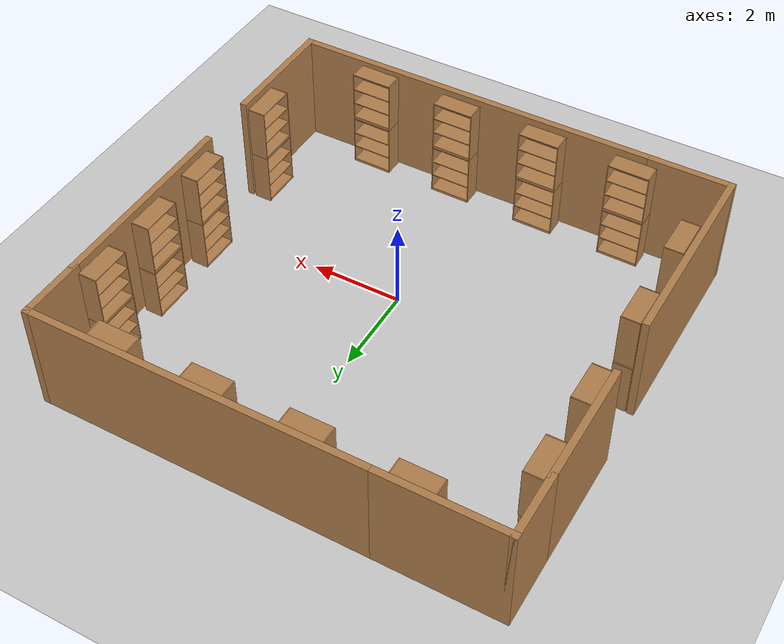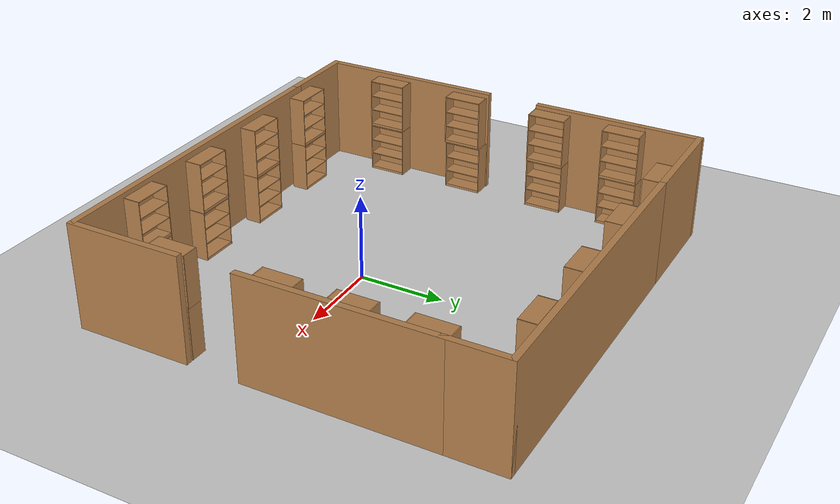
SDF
<sdf version="1.6">
 <world name="default">
  <light name="sun" type="directional">
   <pose>0 0 10 0 -0 0</pose>
   <diffuse>0.8 0.8 0.8 1</diffuse>
   <specular>0.1 0.1 0.1 1</specular>
   <attenuation>
    <range>1000</range>
    <constant>0.9</constant>
    <linear>0.01</linear>
    <quadratic>0.001</quadratic>
   </attenuation>
   <direction>-0.5 0.5 -1</direction>
  </light>
  <model name="ground_plane">
   <static>1</static>
   <link name="link">
    <collision name="collision">
     <geometry><plane><normal>0 0 1</normal><size>100 100</size></plane></geometry>
     <surface><friction><ode><mu>100</mu><mu2>50</mu2></ode></friction></surface>
    </collision>
    <visual name="visual">
     <cast_shadows>0</cast_shadows>
     <geometry><plane><normal>0 0 1</normal><size>100 100</size></plane></geometry>
     <material>
      <script><uri>file://media/materials/scripts/gazebo.material</uri><name>Gazebo/Grey</name></script>
     </material>
    </visual>
   </link>
  </model>
  <gravity>0 0 -9.8</gravity>
  <magnetic_field>6e-06 2.3e-05 -4.2e-05</magnetic_field>
  <atmosphere type="adiabatic"/>
  <physics name="default_physics" default="0" type="ode">
   <max_step_size>0.001</max_step_size>
   <real_time_factor>1</real_time_factor>
   <real_time_update_rate>1000</real_time_update_rate>
  </physics>
  <scene><ambient>0.4 0.4 0.4 1</ambient><background>0.7 0.7 0.7 1</background><shadows>1</shadows></scene>
  <spherical_coordinates>
   <surface_model>EARTH_WGS84</surface_model>
   <latitude_deg>0</latitude_deg>
   <longitude_deg>0</longitude_deg>
   <elevation>0</elevation>
   <heading_deg>0</heading_deg>
  </spherical_coordinates>
  <model name="shopping_mart_box">
   <pose>-0.44063 0.87202 0 0 -0 0</pose>
   <link name="Wall_11">
    <collision name="Wall_11_Collision">
     <geometry><box><size>2 0.15 2.5</size></box></geometry>
     <pose>0 0 1.25 0 -0 0</pose>
    </collision>
    <visual name="Wall_11_Visual">
     <pose>0 0 1.25 0 -0 0</pose>
     <geometry><box><size>2 0.15 2.5</size></box></geometry>
     <material>
      <script><uri>file://media/materials/scripts/gazebo.material</uri><name>Gazebo/Wood</name></script>
      <ambient>1 1 1 1</ambient>
     </material>
    </visual>
    <pose>-4.05 -4.85 0 0 -0 3.14159</pose>
   </link>
   <link name="Wall_12">
    <collision name="Wall_12_Collision">
     <geometry><box><size>4.5 0.15 2.5</size></box></geometry>
     <pose>0 0 1.25 0 -0 0</pose>
    </collision>
    <visual name="Wall_12_Visual">
     <pose>0 0 1.25 0 -0 0</pose>
     <geometry><box><size>4.5 0.15 2.5</size></box></geometry>
     <material>
      <script><uri>file://media/materials/scripts/gazebo.material</uri><name>Gazebo/Wood</name></script>
      <ambient>1 1 1 1</ambient>
     </material>
    </visual>
    <pose>-4.975 -2.675 0 0 -0 1.5708</pose>
   </link>
   <link name="Wall_15">
    <collision name="Wall_15_Collision">
     <geometry><box><size>2.75 0.15 2.5</size></box></geometry>
     <pose>0 0 1.25 0 -0 0</pose>
    </collision>
    <visual name="Wall_15_Visual">
     <pose>0 0 1.25 0 -0 0</pose>
     <geometry><box><size>2.75 0.15 2.5</size></box></geometry>
     <material>
      <script><uri>file://media/materials/scripts/gazebo.material</uri><name>Gazebo/Wood</name></script>
      <ambient>1 1 1 1</ambient>
     </material>
    </visual>
    <pose>-4.975 2.2 0 0 0 -1.5708</pose>
   </link>
   <link name="Wall_17">
    <collision name="Wall_17_Collision">
     <geometry><box><size>1.5 0.15 2.5</size></box></geometry>
     <pose>0 0 1.25 0 -0 0</pose>
    </collision>
    <visual name="Wall_17_Visual">
     <pose>0 0 1.25 0 -0 0</pose>
     <geometry><box><size>1.5 0.15 2.5</size></box></geometry>
     <material>
      <script><uri>file://media/materials/scripts/gazebo.material</uri><name>Gazebo/Wood</name></script>
      <ambient>1 1 1 1</ambient>
     </material>
    </visual>
    <pose>-4.975 4.175 0 0 -0 1.5708</pose>
   </link>
   <link name="Wall_21">
    <collision name="Wall_21_Collision">
     <geometry><box><size>2.75 0.15 2.5</size></box></geometry>
     <pose>0 0 1.25 0 -0 0</pose>
    </collision>
    <visual name="Wall_21_Visual">
     <pose>0 0 1.25 0 -0 0</pose>
     <geometry><box><size>2.75 0.15 2.5</size></box></geometry>
     <material>
      <script><uri>file://media/materials/scripts/gazebo.material</uri><name>Gazebo/Wood</name></script>
      <ambient>1 1 1 1</ambient>
     </material>
    </visual>
    <pose>-3.675 4.85 0 0 -0 0</pose>
   </link>
   <link name="Wall_22">
    <collision name="Wall_22_Collision">
     <geometry><box><size>7.5 0.15 2.5</size></box></geometry>
     <pose>0 0 1.25 0 -0 0</pose>
    </collision>
    <visual name="Wall_22_Visual">
     <pose>0 0 1.25 0 -0 0</pose>
     <geometry><box><size>7.5 0.15 2.5</size></box></geometry>
     <material>
      <script><uri>file://media/materials/scripts/gazebo.material</uri><name>Gazebo/Wood</name></script>
      <ambient>1 1 1 1</ambient>
     </material>
    </visual>
    <pose>1.3 4.85 0 0 -0 0</pose>
   </link>
   <link name="Wall_23">
    <collision name="Wall_23_Collision">
     <geometry><box><size>1.5 0.15 2.5</size></box></geometry>
     <pose>0 0 1.25 0 -0 0</pose>
    </collision>
    <visual name="Wall_23_Visual">
     <pose>0 0 1.25 0 -0 0</pose>
     <geometry><box><size>1.5 0.15 2.5</size></box></geometry>
     <material>
      <script><uri>file://media/materials/scripts/gazebo.material</uri><name>Gazebo/Wood</name></script>
      <ambient>1 1 1 1</ambient>
     </material>
    </visual>
    <pose>4.975 4.175 0 0 0 -1.5708</pose>
   </link>
   <link name="Wall_29">
    <collision name="Wall_29_Collision">
     <geometry><box><size>4.5 0.15 2.5</size></box></geometry>
     <pose>0 0 1.25 0 -0 0</pose>
    </collision>
    <visual name="Wall_29_Visual">
     <pose>0 0 1.25 0 -0 0</pose>
     <geometry><box><size>4.5 0.15 2.5</size></box></geometry>
     <material>
      <script><uri>file://media/materials/scripts/gazebo.material</uri><name>Gazebo/Wood</name></script>
      <ambient>1 1 1 1</ambient>
     </material>
    </visual>
    <pose>4.975 1.325 0 0 0 -1.5708</pose>
   </link>
   <link name="Wall_31">
    <collision name="Wall_31_Collision">
     <geometry><box><size>2.75 0.15 2.5</size></box></geometry>
     <pose>0 0 1.25 0 -0 0</pose>
    </collision>
    <visual name="Wall_31_Visual">
     <pose>0 0 1.25 0 -0 0</pose>
     <geometry><box><size>2.75 0.15 2.5</size></box></geometry>
     <material>
      <script><uri>file://media/materials/scripts/gazebo.material</uri><name>Gazebo/Wood</name></script>
      <ambient>1 1 1 1</ambient>
     </material>
    </visual>
    <pose>4.975 -3.55 0 0 -0 1.5708</pose>
   </link>
   <link name="Wall_6">
    <collision name="Wall_6_Collision">
     <geometry><box><size>8.25 0.15 2.5</size></box></geometry>
     <pose>0 0 1.25 0 -0 0</pose>
    </collision>
    <visual name="Wall_6_Visual">
     <pose>0 0 1.25 0 -0 0</pose>
     <geometry><box><size>8.25 0.15 2.5</size></box></geometry>
     <material>
      <script><uri>file://media/materials/scripts/gazebo.material</uri><name>Gazebo/Wood</name></script>
      <ambient>1 1 1 1</ambient>
     </material>
    </visual>
    <pose>0.925 -4.85 0 0 -0 0</pose>
   </link>
   <static>1</static>
  </model>
  <model name="bookshelf">
   <static>1</static>
   <link name="link">
    <inertial><mass>1</mass></inertial>
    <collision name="back">
     <pose>0 0.005 0.6 0 -0 0</pose>
     <geometry><box><size>0.9 0.01 1.2</size></box></geometry>
    </collision>
    <visual name="visual1">
     <pose>0 0.005 0.6 0 -0 0</pose>
     <geometry><box><size>0.9 0.01 1.2</size></box></geometry>
     <material>
      <script><uri>file://media/materials/scripts/gazebo.material</uri><name>Gazebo/Wood</name></script>
     </material>
    </visual>
    <collision name="left_side">
     <pose>0.45 -0.195 0.6 0 -0 0</pose>
     <geometry><box><size>0.02 0.4 1.2</size></box></geometry>
    </collision>
    <visual name="visual2">
     <pose>0.45 -0.195 0.6 0 -0 0</pose>
     <geometry><box><size>0.02 0.4 1.2</size></box></geometry>
     <material>
      <script><uri>file://media/materials/scripts/gazebo.material</uri><name>Gazebo/Wood</name></script>
     </material>
    </visual>
    <collision name="right_side">
     <pose>-0.45 -0.195 0.6 0 -0 0</pose>
     <geometry><box><size>0.02 0.4 1.2</size></box></geometry>
    </collision>
    <visual name="visual3">
     <pose>-0.45 -0.195 0.6 0 -0 0</pose>
     <geometry><box><size>0.02 0.4 1.2</size></box></geometry>
     <material>
      <script><uri>file://media/materials/scripts/gazebo.material</uri><name>Gazebo/Wood</name></script>
     </material>
    </visual>
    <collision name="bottom">
     <pose>0 -0.195 0.03 0 -0 0</pose>
     <geometry><box><size>0.88 0.4 0.06</size></box></geometry>
    </collision>
    <visual name="visual4">
     <pose>0 -0.195 0.03 0 -0 0</pose>
     <geometry><box><size>0.88 0.4 0.06</size></box></geometry>
     <material>
      <script><uri>file://media/materials/scripts/gazebo.material</uri><name>Gazebo/Wood</name></script>
     </material>
    </visual>
    <collision name="top">
     <pose>0 -0.195 1.19 0 -0 0</pose>
     <geometry><box><size>0.88 0.4 0.02</size></box></geometry>
    </collision>
    <visual name="visual5">
     <pose>0 -0.195 1.19 0 -0 0</pose>
     <geometry><box><size>0.88 0.4 0.02</size></box></geometry>
     <material>
      <script><uri>file://media/materials/scripts/gazebo.material</uri><name>Gazebo/Wood</name></script>
     </material>
    </visual>
    <collision name="low_shelf">
     <pose>0 -0.195 0.43 0 -0 0</pose>
     <geometry><box><size>0.88 0.4 0.02</size></box></geometry>
    </collision>
    <visual name="visual6">
     <pose>0 -0.195 0.43 0 -0 0</pose>
     <geometry><box><size>0.88 0.4 0.02</size></box></geometry>
     <material>
      <script><uri>file://media/materials/scripts/gazebo.material</uri><name>Gazebo/Wood</name></script>
     </material>
    </visual>
    <collision name="high_shelf">
     <pose>0 -0.195 0.8 0 -0 0</pose>
     <geometry><box><size>0.88 0.4 0.02</size></box></geometry>
    </collision>
    <visual name="visual7">
     <pose>0 -0.195 0.8 0 -0 0</pose>
     <geometry><box><size>0.88 0.4 0.02</size></box></geometry>
     <material>
      <script><uri>file://media/materials/scripts/gazebo.material</uri><name>Gazebo/Wood</name></script>
     </material>
    </visual>
   </link>
   <pose>2.83268 5.58259 0 0 -0 0</pose>
  </model>
  <model name="bookshelf_1">
   <static>1</static>
   <link name="link">
    <inertial><mass>1</mass></inertial>
    <collision name="back">
     <pose>0 0.005 0.6 0 -0 0</pose>
     <geometry><box><size>0.9 0.01 1.2</size></box></geometry>
    </collision>
    <visual name="visual1">
     <pose>0 0.005 0.6 0 -0 0</pose>
     <geometry><box><size>0.9 0.01 1.2</size></box></geometry>
     <material>
      <script><uri>file://media/materials/scripts/gazebo.material</uri><name>Gazebo/Wood</name></script>
     </material>
    </visual>
    <collision name="left_side">
     <pose>0.45 -0.195 0.6 0 -0 0</pose>
     <geometry><box><size>0.02 0.4 1.2</size></box></geometry>
    </collision>
    <visual name="visual2">
     <pose>0.45 -0.195 0.6 0 -0 0</pose>
     <geometry><box><size>0.02 0.4 1.2</size></box></geometry>
     <material>
      <script><uri>file://media/materials/scripts/gazebo.material</uri><name>Gazebo/Wood</name></script>
     </material>
    </visual>
    <collision name="right_side">
     <pose>-0.45 -0.195 0.6 0 -0 0</pose>
     <geometry><box><size>0.02 0.4 1.2</size></box></geometry>
    </collision>
    <visual name="visual3">
     <pose>-0.45 -0.195 0.6 0 -0 0</pose>
     <geometry><box><size>0.02 0.4 1.2</size></box></geometry>
     <material>
      <script><uri>file://media/materials/scripts/gazebo.material</uri><name>Gazebo/Wood</name></script>
     </material>
    </visual>
    <collision name="bottom">
     <pose>0 -0.195 0.03 0 -0 0</pose>
     <geometry><box><size>0.88 0.4 0.06</size></box></geometry>
    </collision>
    <visual name="visual4">
     <pose>0 -0.195 0.03 0 -0 0</pose>
     <geometry><box><size>0.88 0.4 0.06</size></box></geometry>
     <material>
      <script><uri>file://media/materials/scripts/gazebo.material</uri><name>Gazebo/Wood</name></script>
     </material>
    </visual>
    <collision name="top">
     <pose>0 -0.195 1.19 0 -0 0</pose>
     <geometry><box><size>0.88 0.4 0.02</size></box></geometry>
    </collision>
    <visual name="visual5">
     <pose>0 -0.195 1.19 0 -0 0</pose>
     <geometry><box><size>0.88 0.4 0.02</size></box></geometry>
     <material>
      <script><uri>file://media/materials/scripts/gazebo.material</uri><name>Gazebo/Wood</name></script>
     </material>
    </visual>
    <collision name="low_shelf">
     <pose>0 -0.195 0.43 0 -0 0</pose>
     <geometry><box><size>0.88 0.4 0.02</size></box></geometry>
    </collision>
    <visual name="visual6">
     <pose>0 -0.195 0.43 0 -0 0</pose>
     <geometry><box><size>0.88 0.4 0.02</size></box></geometry>
     <material>
      <script><uri>file://media/materials/scripts/gazebo.material</uri><name>Gazebo/Wood</name></script>
     </material>
    </visual>
    <collision name="high_shelf">
     <pose>0 -0.195 0.8 0 -0 0</pose>
     <geometry><box><size>0.88 0.4 0.02</size></box></geometry>
    </collision>
    <visual name="visual7">
     <pose>0 -0.195 0.8 0 -0 0</pose>
     <geometry><box><size>0.88 0.4 0.02</size></box></geometry>
     <material>
      <script><uri>file://media/materials/scripts/gazebo.material</uri><name>Gazebo/Wood</name></script>
     </material>
    </visual>
   </link>
   <pose>0.770602 5.5901 0 0 -0 0</pose>
  </model>
  <model name="bookshelf_2_clone">
   <static>1</static>
   <link name="link">
    <inertial><mass>1</mass></inertial>
    <collision name="back">
     <pose>0 0.005 0.6 0 -0 0</pose>
     <geometry><box><size>0.9 0.01 1.2</size></box></geometry>
    </collision>
    <visual name="visual1">
     <pose>0 0.005 0.6 0 -0 0</pose>
     <geometry><box><size>0.9 0.01 1.2</size></box></geometry>
     <material>
      <script><uri>file://media/materials/scripts/gazebo.material</uri><name>Gazebo/Wood</name></script>
     </material>
    </visual>
    <collision name="left_side">
     <pose>0.45 -0.195 0.6 0 -0 0</pose>
     <geometry><box><size>0.02 0.4 1.2</size></box></geometry>
    </collision>
    <visual name="visual2">
     <pose>0.45 -0.195 0.6 0 -0 0</pose>
     <geometry><box><size>0.02 0.4 1.2</size></box></geometry>
     <material>
      <script><uri>file://media/materials/scripts/gazebo.material</uri><name>Gazebo/Wood</name></script>
     </material>
    </visual>
    <collision name="right_side">
     <pose>-0.45 -0.195 0.6 0 -0 0</pose>
     <geometry><box><size>0.02 0.4 1.2</size></box></geometry>
    </collision>
    <visual name="visual3">
     <pose>-0.45 -0.195 0.6 0 -0 0</pose>
     <geometry><box><size>0.02 0.4 1.2</size></box></geometry>
     <material>
      <script><uri>file://media/materials/scripts/gazebo.material</uri><name>Gazebo/Wood</name></script>
     </material>
    </visual>
    <collision name="bottom">
     <pose>0 -0.195 0.03 0 -0 0</pose>
     <geometry><box><size>0.88 0.4 0.06</size></box></geometry>
    </collision>
    <visual name="visual4">
     <pose>0 -0.195 0.03 0 -0 0</pose>
     <geometry><box><size>0.88 0.4 0.06</size></box></geometry>
     <material>
      <script><uri>file://media/materials/scripts/gazebo.material</uri><name>Gazebo/Wood</name></script>
     </material>
    </visual>
    <collision name="top">
     <pose>0 -0.195 1.19 0 -0 0</pose>
     <geometry><box><size>0.88 0.4 0.02</size></box></geometry>
    </collision>
    <visual name="visual5">
     <pose>0 -0.195 1.19 0 -0 0</pose>
     <geometry><box><size>0.88 0.4 0.02</size></box></geometry>
     <material>
      <script><uri>file://media/materials/scripts/gazebo.material</uri><name>Gazebo/Wood</name></script>
     </material>
    </visual>
    <collision name="low_shelf">
     <pose>0 -0.195 0.43 0 -0 0</pose>
     <geometry><box><size>0.88 0.4 0.02</size></box></geometry>
    </collision>
    <visual name="visual6">
     <pose>0 -0.195 0.43 0 -0 0</pose>
     <geometry><box><size>0.88 0.4 0.02</size></box></geometry>
     <material>
      <script><uri>file://media/materials/scripts/gazebo.material</uri><name>Gazebo/Wood</name></script>
     </material>
    </visual>
    <collision name="high_shelf">
     <pose>0 -0.195 0.8 0 -0 0</pose>
     <geometry><box><size>0.88 0.4 0.02</size></box></geometry>
    </collision>
    <visual name="visual7">
     <pose>0 -0.195 0.8 0 -0 0</pose>
     <geometry><box><size>0.88 0.4 0.02</size></box></geometry>
     <material>
      <script><uri>file://media/materials/scripts/gazebo.material</uri><name>Gazebo/Wood</name></script>
     </material>
    </visual>
   </link>
   <pose>-1.30264 5.59901 0 0 -0 0</pose>
  </model>
  <model name="bookshelf_2_clone_clone">
   <static>1</static>
   <link name="link">
    <inertial><mass>1</mass></inertial>
    <collision name="back">
     <pose>0 0.005 0.6 0 -0 0</pose>
     <geometry><box><size>0.9 0.01 1.2</size></box></geometry>
    </collision>
    <visual name="visual1">
     <pose>0 0.005 0.6 0 -0 0</pose>
     <geometry><box><size>0.9 0.01 1.2</size></box></geometry>
     <material>
      <script><uri>file://media/materials/scripts/gazebo.material</uri><name>Gazebo/Wood</name></script>
     </material>
    </visual>
    <collision name="left_side">
     <pose>0.45 -0.195 0.6 0 -0 0</pose>
     <geometry><box><size>0.02 0.4 1.2</size></box></geometry>
    </collision>
    <visual name="visual2">
     <pose>0.45 -0.195 0.6 0 -0 0</pose>
     <geometry><box><size>0.02 0.4 1.2</size></box></geometry>
     <material>
      <script><uri>file://media/materials/scripts/gazebo.material</uri><name>Gazebo/Wood</name></script>
     </material>
    </visual>
    <collision name="right_side">
     <pose>-0.45 -0.195 0.6 0 -0 0</pose>
     <geometry><box><size>0.02 0.4 1.2</size></box></geometry>
    </collision>
    <visual name="visual3">
     <pose>-0.45 -0.195 0.6 0 -0 0</pose>
     <geometry><box><size>0.02 0.4 1.2</size></box></geometry>
     <material>
      <script><uri>file://media/materials/scripts/gazebo.material</uri><name>Gazebo/Wood</name></script>
     </material>
    </visual>
    <collision name="bottom">
     <pose>0 -0.195 0.03 0 -0 0</pose>
     <geometry><box><size>0.88 0.4 0.06</size></box></geometry>
    </collision>
    <visual name="visual4">
     <pose>0 -0.195 0.03 0 -0 0</pose>
     <geometry><box><size>0.88 0.4 0.06</size></box></geometry>
     <material>
      <script><uri>file://media/materials/scripts/gazebo.material</uri><name>Gazebo/Wood</name></script>
     </material>
    </visual>
    <collision name="top">
     <pose>0 -0.195 1.19 0 -0 0</pose>
     <geometry><box><size>0.88 0.4 0.02</size></box></geometry>
    </collision>
    <visual name="visual5">
     <pose>0 -0.195 1.19 0 -0 0</pose>
     <geometry><box><size>0.88 0.4 0.02</size></box></geometry>
     <material>
      <script><uri>file://media/materials/scripts/gazebo.material</uri><name>Gazebo/Wood</name></script>
     </material>
    </visual>
    <collision name="low_shelf">
     <pose>0 -0.195 0.43 0 -0 0</pose>
     <geometry><box><size>0.88 0.4 0.02</size></box></geometry>
    </collision>
    <visual name="visual6">
     <pose>0 -0.195 0.43 0 -0 0</pose>
     <geometry><box><size>0.88 0.4 0.02</size></box></geometry>
     <material>
      <script><uri>file://media/materials/scripts/gazebo.material</uri><name>Gazebo/Wood</name></script>
     </material>
    </visual>
    <collision name="high_shelf">
     <pose>0 -0.195 0.8 0 -0 0</pose>
     <geometry><box><size>0.88 0.4 0.02</size></box></geometry>
    </collision>
    <visual name="visual7">
     <pose>0 -0.195 0.8 0 -0 0</pose>
     <geometry><box><size>0.88 0.4 0.02</size></box></geometry>
     <material>
      <script><uri>file://media/materials/scripts/gazebo.material</uri><name>Gazebo/Wood</name></script>
     </material>
    </visual>
   </link>
   <pose>-3.46853 5.62428 0 0 -0 0</pose>
  </model>
  <model name="bookshelf_3_clone">
   <static>1</static>
   <link name="link">
    <inertial><mass>1</mass></inertial>
    <collision name="back">
     <pose>0 0.005 0.6 0 -0 0</pose>
     <geometry><box><size>0.9 0.01 1.2</size></box></geometry>
    </collision>
    <visual name="visual1">
     <pose>0 0.005 0.6 0 -0 0</pose>
     <geometry><box><size>0.9 0.01 1.2</size></box></geometry>
     <material>
      <script><uri>file://media/materials/scripts/gazebo.material</uri><name>Gazebo/Wood</name></script>
     </material>
    </visual>
    <collision name="left_side">
     <pose>0.45 -0.195 0.6 0 -0 0</pose>
     <geometry><box><size>0.02 0.4 1.2</size></box></geometry>
    </collision>
    <visual name="visual2">
     <pose>0.45 -0.195 0.6 0 -0 0</pose>
     <geometry><box><size>0.02 0.4 1.2</size></box></geometry>
     <material>
      <script><uri>file://media/materials/scripts/gazebo.material</uri><name>Gazebo/Wood</name></script>
     </material>
    </visual>
    <collision name="right_side">
     <pose>-0.45 -0.195 0.6 0 -0 0</pose>
     <geometry><box><size>0.02 0.4 1.2</size></box></geometry>
    </collision>
    <visual name="visual3">
     <pose>-0.45 -0.195 0.6 0 -0 0</pose>
     <geometry><box><size>0.02 0.4 1.2</size></box></geometry>
     <material>
      <script><uri>file://media/materials/scripts/gazebo.material</uri><name>Gazebo/Wood</name></script>
     </material>
    </visual>
    <collision name="bottom">
     <pose>0 -0.195 0.03 0 -0 0</pose>
     <geometry><box><size>0.88 0.4 0.06</size></box></geometry>
    </collision>
    <visual name="visual4">
     <pose>0 -0.195 0.03 0 -0 0</pose>
     <geometry><box><size>0.88 0.4 0.06</size></box></geometry>
     <material>
      <script><uri>file://media/materials/scripts/gazebo.material</uri><name>Gazebo/Wood</name></script>
     </material>
    </visual>
    <collision name="top">
     <pose>0 -0.195 1.19 0 -0 0</pose>
     <geometry><box><size>0.88 0.4 0.02</size></box></geometry>
    </collision>
    <visual name="visual5">
     <pose>0 -0.195 1.19 0 -0 0</pose>
     <geometry><box><size>0.88 0.4 0.02</size></box></geometry>
     <material>
      <script><uri>file://media/materials/scripts/gazebo.material</uri><name>Gazebo/Wood</name></script>
     </material>
    </visual>
    <collision name="low_shelf">
     <pose>0 -0.195 0.43 0 -0 0</pose>
     <geometry><box><size>0.88 0.4 0.02</size></box></geometry>
    </collision>
    <visual name="visual6">
     <pose>0 -0.195 0.43 0 -0 0</pose>
     <geometry><box><size>0.88 0.4 0.02</size></box></geometry>
     <material>
      <script><uri>file://media/materials/scripts/gazebo.material</uri><name>Gazebo/Wood</name></script>
     </material>
    </visual>
    <collision name="high_shelf">
     <pose>0 -0.195 0.8 0 -0 0</pose>
     <geometry><box><size>0.88 0.4 0.02</size></box></geometry>
    </collision>
    <visual name="visual7">
     <pose>0 -0.195 0.8 0 -0 0</pose>
     <geometry><box><size>0.88 0.4 0.02</size></box></geometry>
     <material>
      <script><uri>file://media/materials/scripts/gazebo.material</uri><name>Gazebo/Wood</name></script>
     </material>
    </visual>
   </link>
   <pose>-1.30336 5.6079 1.20481 0 -0 0</pose>
  </model>
  <model name="bookshelf_3_clone_clone">
   <static>1</static>
   <link name="link">
    <inertial><mass>1</mass></inertial>
    <collision name="back">
     <pose>0 0.005 0.6 0 -0 0</pose>
     <geometry><box><size>0.9 0.01 1.2</size></box></geometry>
    </collision>
    <visual name="visual1">
     <pose>0 0.005 0.6 0 -0 0</pose>
     <geometry><box><size>0.9 0.01 1.2</size></box></geometry>
     <material>
      <script><uri>file://media/materials/scripts/gazebo.material</uri><name>Gazebo/Wood</name></script>
     </material>
    </visual>
    <collision name="left_side">
     <pose>0.45 -0.195 0.6 0 -0 0</pose>
     <geometry><box><size>0.02 0.4 1.2</size></box></geometry>
    </collision>
    <visual name="visual2">
     <pose>0.45 -0.195 0.6 0 -0 0</pose>
     <geometry><box><size>0.02 0.4 1.2</size></box></geometry>
     <material>
      <script><uri>file://media/materials/scripts/gazebo.material</uri><name>Gazebo/Wood</name></script>
     </material>
    </visual>
    <collision name="right_side">
     <pose>-0.45 -0.195 0.6 0 -0 0</pose>
     <geometry><box><size>0.02 0.4 1.2</size></box></geometry>
    </collision>
    <visual name="visual3">
     <pose>-0.45 -0.195 0.6 0 -0 0</pose>
     <geometry><box><size>0.02 0.4 1.2</size></box></geometry>
     <material>
      <script><uri>file://media/materials/scripts/gazebo.material</uri><name>Gazebo/Wood</name></script>
     </material>
    </visual>
    <collision name="bottom">
     <pose>0 -0.195 0.03 0 -0 0</pose>
     <geometry><box><size>0.88 0.4 0.06</size></box></geometry>
    </collision>
    <visual name="visual4">
     <pose>0 -0.195 0.03 0 -0 0</pose>
     <geometry><box><size>0.88 0.4 0.06</size></box></geometry>
     <material>
      <script><uri>file://media/materials/scripts/gazebo.material</uri><name>Gazebo/Wood</name></script>
     </material>
    </visual>
    <collision name="top">
     <pose>0 -0.195 1.19 0 -0 0</pose>
     <geometry><box><size>0.88 0.4 0.02</size></box></geometry>
    </collision>
    <visual name="visual5">
     <pose>0 -0.195 1.19 0 -0 0</pose>
     <geometry><box><size>0.88 0.4 0.02</size></box></geometry>
     <material>
      <script><uri>file://media/materials/scripts/gazebo.material</uri><name>Gazebo/Wood</name></script>
     </material>
    </visual>
    <collision name="low_shelf">
     <pose>0 -0.195 0.43 0 -0 0</pose>
     <geometry><box><size>0.88 0.4 0.02</size></box></geometry>
    </collision>
    <visual name="visual6">
     <pose>0 -0.195 0.43 0 -0 0</pose>
     <geometry><box><size>0.88 0.4 0.02</size></box></geometry>
     <material>
      <script><uri>file://media/materials/scripts/gazebo.material</uri><name>Gazebo/Wood</name></script>
     </material>
    </visual>
    <collision name="high_shelf">
     <pose>0 -0.195 0.8 0 -0 0</pose>
     <geometry><box><size>0.88 0.4 0.02</size></box></geometry>
    </collision>
    <visual name="visual7">
     <pose>0 -0.195 0.8 0 -0 0</pose>
     <geometry><box><size>0.88 0.4 0.02</size></box></geometry>
     <material>
      <script><uri>file://media/materials/scripts/gazebo.material</uri><name>Gazebo/Wood</name></script>
     </material>
    </visual>
   </link>
   <pose>-3.47373 5.62521 1.20481 0 -0 0</pose>
  </model>
  <model name="bookshelf_3_clone_clone_0">
   <static>1</static>
   <link name="link">
    <inertial><mass>1</mass></inertial>
    <collision name="back">
     <pose>0 0.005 0.6 0 -0 0</pose>
     <geometry><box><size>0.9 0.01 1.2</size></box></geometry>
    </collision>
    <visual name="visual1">
     <pose>0 0.005 0.6 0 -0 0</pose>
     <geometry><box><size>0.9 0.01 1.2</size></box></geometry>
     <material>
      <script><uri>file://media/materials/scripts/gazebo.material</uri><name>Gazebo/Wood</name></script>
     </material>
    </visual>
    <collision name="left_side">
     <pose>0.45 -0.195 0.6 0 -0 0</pose>
     <geometry><box><size>0.02 0.4 1.2</size></box></geometry>
    </collision>
    <visual name="visual2">
     <pose>0.45 -0.195 0.6 0 -0 0</pose>
     <geometry><box><size>0.02 0.4 1.2</size></box></geometry>
     <material>
      <script><uri>file://media/materials/scripts/gazebo.material</uri><name>Gazebo/Wood</name></script>
     </material>
    </visual>
    <collision name="right_side">
     <pose>-0.45 -0.195 0.6 0 -0 0</pose>
     <geometry><box><size>0.02 0.4 1.2</size></box></geometry>
    </collision>
    <visual name="visual3">
     <pose>-0.45 -0.195 0.6 0 -0 0</pose>
     <geometry><box><size>0.02 0.4 1.2</size></box></geometry>
     <material>
      <script><uri>file://media/materials/scripts/gazebo.material</uri><name>Gazebo/Wood</name></script>
     </material>
    </visual>
    <collision name="bottom">
     <pose>0 -0.195 0.03 0 -0 0</pose>
     <geometry><box><size>0.88 0.4 0.06</size></box></geometry>
    </collision>
    <visual name="visual4">
     <pose>0 -0.195 0.03 0 -0 0</pose>
     <geometry><box><size>0.88 0.4 0.06</size></box></geometry>
     <material>
      <script><uri>file://media/materials/scripts/gazebo.material</uri><name>Gazebo/Wood</name></script>
     </material>
    </visual>
    <collision name="top">
     <pose>0 -0.195 1.19 0 -0 0</pose>
     <geometry><box><size>0.88 0.4 0.02</size></box></geometry>
    </collision>
    <visual name="visual5">
     <pose>0 -0.195 1.19 0 -0 0</pose>
     <geometry><box><size>0.88 0.4 0.02</size></box></geometry>
     <material>
      <script><uri>file://media/materials/scripts/gazebo.material</uri><name>Gazebo/Wood</name></script>
     </material>
    </visual>
    <collision name="low_shelf">
     <pose>0 -0.195 0.43 0 -0 0</pose>
     <geometry><box><size>0.88 0.4 0.02</size></box></geometry>
    </collision>
    <visual name="visual6">
     <pose>0 -0.195 0.43 0 -0 0</pose>
     <geometry><box><size>0.88 0.4 0.02</size></box></geometry>
     <material>
      <script><uri>file://media/materials/scripts/gazebo.material</uri><name>Gazebo/Wood</name></script>
     </material>
    </visual>
    <collision name="high_shelf">
     <pose>0 -0.195 0.8 0 -0 0</pose>
     <geometry><box><size>0.88 0.4 0.02</size></box></geometry>
    </collision>
    <visual name="visual7">
     <pose>0 -0.195 0.8 0 -0 0</pose>
     <geometry><box><size>0.88 0.4 0.02</size></box></geometry>
     <material>
      <script><uri>file://media/materials/scripts/gazebo.material</uri><name>Gazebo/Wood</name></script>
     </material>
    </visual>
   </link>
   <pose>0.76852 5.59426 1.20481 0 -0 0</pose>
  </model>
  <model name="bookshelf_3_clone_clone_1">
   <static>1</static>
   <link name="link">
    <inertial><mass>1</mass></inertial>
    <collision name="back">
     <pose>0 0.005 0.6 0 -0 0</pose>
     <geometry><box><size>0.9 0.01 1.2</size></box></geometry>
    </collision>
    <visual name="visual1">
     <pose>0 0.005 0.6 0 -0 0</pose>
     <geometry><box><size>0.9 0.01 1.2</size></box></geometry>
     <material>
      <script><uri>file://media/materials/scripts/gazebo.material</uri><name>Gazebo/Wood</name></script>
     </material>
    </visual>
    <collision name="left_side">
     <pose>0.45 -0.195 0.6 0 -0 0</pose>
     <geometry><box><size>0.02 0.4 1.2</size></box></geometry>
    </collision>
    <visual name="visual2">
     <pose>0.45 -0.195 0.6 0 -0 0</pose>
     <geometry><box><size>0.02 0.4 1.2</size></box></geometry>
     <material>
      <script><uri>file://media/materials/scripts/gazebo.material</uri><name>Gazebo/Wood</name></script>
     </material>
    </visual>
    <collision name="right_side">
     <pose>-0.45 -0.195 0.6 0 -0 0</pose>
     <geometry><box><size>0.02 0.4 1.2</size></box></geometry>
    </collision>
    <visual name="visual3">
     <pose>-0.45 -0.195 0.6 0 -0 0</pose>
     <geometry><box><size>0.02 0.4 1.2</size></box></geometry>
     <material>
      <script><uri>file://media/materials/scripts/gazebo.material</uri><name>Gazebo/Wood</name></script>
     </material>
    </visual>
    <collision name="bottom">
     <pose>0 -0.195 0.03 0 -0 0</pose>
     <geometry><box><size>0.88 0.4 0.06</size></box></geometry>
    </collision>
    <visual name="visual4">
     <pose>0 -0.195 0.03 0 -0 0</pose>
     <geometry><box><size>0.88 0.4 0.06</size></box></geometry>
     <material>
      <script><uri>file://media/materials/scripts/gazebo.material</uri><name>Gazebo/Wood</name></script>
     </material>
    </visual>
    <collision name="top">
     <pose>0 -0.195 1.19 0 -0 0</pose>
     <geometry><box><size>0.88 0.4 0.02</size></box></geometry>
    </collision>
    <visual name="visual5">
     <pose>0 -0.195 1.19 0 -0 0</pose>
     <geometry><box><size>0.88 0.4 0.02</size></box></geometry>
     <material>
      <script><uri>file://media/materials/scripts/gazebo.material</uri><name>Gazebo/Wood</name></script>
     </material>
    </visual>
    <collision name="low_shelf">
     <pose>0 -0.195 0.43 0 -0 0</pose>
     <geometry><box><size>0.88 0.4 0.02</size></box></geometry>
    </collision>
    <visual name="visual6">
     <pose>0 -0.195 0.43 0 -0 0</pose>
     <geometry><box><size>0.88 0.4 0.02</size></box></geometry>
     <material>
      <script><uri>file://media/materials/scripts/gazebo.material</uri><name>Gazebo/Wood</name></script>
     </material>
    </visual>
    <collision name="high_shelf">
     <pose>0 -0.195 0.8 0 -0 0</pose>
     <geometry><box><size>0.88 0.4 0.02</size></box></geometry>
    </collision>
    <visual name="visual7">
     <pose>0 -0.195 0.8 0 -0 0</pose>
     <geometry><box><size>0.88 0.4 0.02</size></box></geometry>
     <material>
      <script><uri>file://media/materials/scripts/gazebo.material</uri><name>Gazebo/Wood</name></script>
     </material>
    </visual>
   </link>
   <pose>2.83627 5.58516 1.20481 0 -0 0</pose>
  </model>
  <model name="bookshelf_4_clone">
   <static>1</static>
   <link name="link">
    <inertial><mass>1</mass></inertial>
    <collision name="back">
     <pose>0 0.005 0.6 0 -0 0</pose>
     <geometry><box><size>0.9 0.01 1.2</size></box></geometry>
    </collision>
    <visual name="visual1">
     <pose>0 0.005 0.6 0 -0 0</pose>
     <geometry><box><size>0.9 0.01 1.2</size></box></geometry>
     <material>
      <script><uri>file://media/materials/scripts/gazebo.material</uri><name>Gazebo/Wood</name></script>
     </material>
    </visual>
    <collision name="left_side">
     <pose>0.45 -0.195 0.6 0 -0 0</pose>
     <geometry><box><size>0.02 0.4 1.2</size></box></geometry>
    </collision>
    <visual name="visual2">
     <pose>0.45 -0.195 0.6 0 -0 0</pose>
     <geometry><box><size>0.02 0.4 1.2</size></box></geometry>
     <material>
      <script><uri>file://media/materials/scripts/gazebo.material</uri><name>Gazebo/Wood</name></script>
     </material>
    </visual>
    <collision name="right_side">
     <pose>-0.45 -0.195 0.6 0 -0 0</pose>
     <geometry><box><size>0.02 0.4 1.2</size></box></geometry>
    </collision>
    <visual name="visual3">
     <pose>-0.45 -0.195 0.6 0 -0 0</pose>
     <geometry><box><size>0.02 0.4 1.2</size></box></geometry>
     <material>
      <script><uri>file://media/materials/scripts/gazebo.material</uri><name>Gazebo/Wood</name></script>
     </material>
    </visual>
    <collision name="bottom">
     <pose>0 -0.195 0.03 0 -0 0</pose>
     <geometry><box><size>0.88 0.4 0.06</size></box></geometry>
    </collision>
    <visual name="visual4">
     <pose>0 -0.195 0.03 0 -0 0</pose>
     <geometry><box><size>0.88 0.4 0.06</size></box></geometry>
     <material>
      <script><uri>file://media/materials/scripts/gazebo.material</uri><name>Gazebo/Wood</name></script>
     </material>
    </visual>
    <collision name="top">
     <pose>0 -0.195 1.19 0 -0 0</pose>
     <geometry><box><size>0.88 0.4 0.02</size></box></geometry>
    </collision>
    <visual name="visual5">
     <pose>0 -0.195 1.19 0 -0 0</pose>
     <geometry><box><size>0.88 0.4 0.02</size></box></geometry>
     <material>
      <script><uri>file://media/materials/scripts/gazebo.material</uri><name>Gazebo/Wood</name></script>
     </material>
    </visual>
    <collision name="low_shelf">
     <pose>0 -0.195 0.43 0 -0 0</pose>
     <geometry><box><size>0.88 0.4 0.02</size></box></geometry>
    </collision>
    <visual name="visual6">
     <pose>0 -0.195 0.43 0 -0 0</pose>
     <geometry><box><size>0.88 0.4 0.02</size></box></geometry>
     <material>
      <script><uri>file://media/materials/scripts/gazebo.material</uri><name>Gazebo/Wood</name></script>
     </material>
    </visual>
    <collision name="high_shelf">
     <pose>0 -0.195 0.8 0 -0 0</pose>
     <geometry><box><size>0.88 0.4 0.02</size></box></geometry>
    </collision>
    <visual name="visual7">
     <pose>0 -0.195 0.8 0 -0 0</pose>
     <geometry><box><size>0.88 0.4 0.02</size></box></geometry>
     <material>
      <script><uri>file://media/materials/scripts/gazebo.material</uri><name>Gazebo/Wood</name></script>
     </material>
    </visual>
   </link>
   <pose>4.37345 3.97883 0 0 0 -1.5727</pose>
  </model>
  <model name="bookshelf_4_clone_0">
   <static>1</static>
   <link name="link">
    <inertial><mass>1</mass></inertial>
    <collision name="back">
     <pose>0 0.005 0.6 0 -0 0</pose>
     <geometry><box><size>0.9 0.01 1.2</size></box></geometry>
    </collision>
    <visual name="visual1">
     <pose>0 0.005 0.6 0 -0 0</pose>
     <geometry><box><size>0.9 0.01 1.2</size></box></geometry>
     <material>
      <script><uri>file://media/materials/scripts/gazebo.material</uri><name>Gazebo/Wood</name></script>
     </material>
    </visual>
    <collision name="left_side">
     <pose>0.45 -0.195 0.6 0 -0 0</pose>
     <geometry><box><size>0.02 0.4 1.2</size></box></geometry>
    </collision>
    <visual name="visual2">
     <pose>0.45 -0.195 0.6 0 -0 0</pose>
     <geometry><box><size>0.02 0.4 1.2</size></box></geometry>
     <material>
      <script><uri>file://media/materials/scripts/gazebo.material</uri><name>Gazebo/Wood</name></script>
     </material>
    </visual>
    <collision name="right_side">
     <pose>-0.45 -0.195 0.6 0 -0 0</pose>
     <geometry><box><size>0.02 0.4 1.2</size></box></geometry>
    </collision>
    <visual name="visual3">
     <pose>-0.45 -0.195 0.6 0 -0 0</pose>
     <geometry><box><size>0.02 0.4 1.2</size></box></geometry>
     <material>
      <script><uri>file://media/materials/scripts/gazebo.material</uri><name>Gazebo/Wood</name></script>
     </material>
    </visual>
    <collision name="bottom">
     <pose>0 -0.195 0.03 0 -0 0</pose>
     <geometry><box><size>0.88 0.4 0.06</size></box></geometry>
    </collision>
    <visual name="visual4">
     <pose>0 -0.195 0.03 0 -0 0</pose>
     <geometry><box><size>0.88 0.4 0.06</size></box></geometry>
     <material>
      <script><uri>file://media/materials/scripts/gazebo.material</uri><name>Gazebo/Wood</name></script>
     </material>
    </visual>
    <collision name="top">
     <pose>0 -0.195 1.19 0 -0 0</pose>
     <geometry><box><size>0.88 0.4 0.02</size></box></geometry>
    </collision>
    <visual name="visual5">
     <pose>0 -0.195 1.19 0 -0 0</pose>
     <geometry><box><size>0.88 0.4 0.02</size></box></geometry>
     <material>
      <script><uri>file://media/materials/scripts/gazebo.material</uri><name>Gazebo/Wood</name></script>
     </material>
    </visual>
    <collision name="low_shelf">
     <pose>0 -0.195 0.43 0 -0 0</pose>
     <geometry><box><size>0.88 0.4 0.02</size></box></geometry>
    </collision>
    <visual name="visual6">
     <pose>0 -0.195 0.43 0 -0 0</pose>
     <geometry><box><size>0.88 0.4 0.02</size></box></geometry>
     <material>
      <script><uri>file://media/materials/scripts/gazebo.material</uri><name>Gazebo/Wood</name></script>
     </material>
    </visual>
    <collision name="high_shelf">
     <pose>0 -0.195 0.8 0 -0 0</pose>
     <geometry><box><size>0.88 0.4 0.02</size></box></geometry>
    </collision>
    <visual name="visual7">
     <pose>0 -0.195 0.8 0 -0 0</pose>
     <geometry><box><size>0.88 0.4 0.02</size></box></geometry>
     <material>
      <script><uri>file://media/materials/scripts/gazebo.material</uri><name>Gazebo/Wood</name></script>
     </material>
    </visual>
   </link>
   <pose>4.37565 2.36025 0 0 0 -1.5727</pose>
  </model>
  <model name="bookshelf_4_clone_1">
   <static>1</static>
   <link name="link">
    <inertial><mass>1</mass></inertial>
    <collision name="back">
     <pose>0 0.005 0.6 0 -0 0</pose>
     <geometry><box><size>0.9 0.01 1.2</size></box></geometry>
    </collision>
    <visual name="visual1">
     <pose>0 0.005 0.6 0 -0 0</pose>
     <geometry><box><size>0.9 0.01 1.2</size></box></geometry>
     <material>
      <script><uri>file://media/materials/scripts/gazebo.material</uri><name>Gazebo/Wood</name></script>
     </material>
    </visual>
    <collision name="left_side">
     <pose>0.45 -0.195 0.6 0 -0 0</pose>
     <geometry><box><size>0.02 0.4 1.2</size></box></geometry>
    </collision>
    <visual name="visual2">
     <pose>0.45 -0.195 0.6 0 -0 0</pose>
     <geometry><box><size>0.02 0.4 1.2</size></box></geometry>
     <material>
      <script><uri>file://media/materials/scripts/gazebo.material</uri><name>Gazebo/Wood</name></script>
     </material>
    </visual>
    <collision name="right_side">
     <pose>-0.45 -0.195 0.6 0 -0 0</pose>
     <geometry><box><size>0.02 0.4 1.2</size></box></geometry>
    </collision>
    <visual name="visual3">
     <pose>-0.45 -0.195 0.6 0 -0 0</pose>
     <geometry><box><size>0.02 0.4 1.2</size></box></geometry>
     <material>
      <script><uri>file://media/materials/scripts/gazebo.material</uri><name>Gazebo/Wood</name></script>
     </material>
    </visual>
    <collision name="bottom">
     <pose>0 -0.195 0.03 0 -0 0</pose>
     <geometry><box><size>0.88 0.4 0.06</size></box></geometry>
    </collision>
    <visual name="visual4">
     <pose>0 -0.195 0.03 0 -0 0</pose>
     <geometry><box><size>0.88 0.4 0.06</size></box></geometry>
     <material>
      <script><uri>file://media/materials/scripts/gazebo.material</uri><name>Gazebo/Wood</name></script>
     </material>
    </visual>
    <collision name="top">
     <pose>0 -0.195 1.19 0 -0 0</pose>
     <geometry><box><size>0.88 0.4 0.02</size></box></geometry>
    </collision>
    <visual name="visual5">
     <pose>0 -0.195 1.19 0 -0 0</pose>
     <geometry><box><size>0.88 0.4 0.02</size></box></geometry>
     <material>
      <script><uri>file://media/materials/scripts/gazebo.material</uri><name>Gazebo/Wood</name></script>
     </material>
    </visual>
    <collision name="low_shelf">
     <pose>0 -0.195 0.43 0 -0 0</pose>
     <geometry><box><size>0.88 0.4 0.02</size></box></geometry>
    </collision>
    <visual name="visual6">
     <pose>0 -0.195 0.43 0 -0 0</pose>
     <geometry><box><size>0.88 0.4 0.02</size></box></geometry>
     <material>
      <script><uri>file://media/materials/scripts/gazebo.material</uri><name>Gazebo/Wood</name></script>
     </material>
    </visual>
    <collision name="high_shelf">
     <pose>0 -0.195 0.8 0 -0 0</pose>
     <geometry><box><size>0.88 0.4 0.02</size></box></geometry>
    </collision>
    <visual name="visual7">
     <pose>0 -0.195 0.8 0 -0 0</pose>
     <geometry><box><size>0.88 0.4 0.02</size></box></geometry>
     <material>
      <script><uri>file://media/materials/scripts/gazebo.material</uri><name>Gazebo/Wood</name></script>
     </material>
    </visual>
   </link>
   <pose>4.39312 0.69592 0 0 0 -1.5727</pose>
  </model>
  <model name="bookshelf_4_clone_1_clone">
   <static>1</static>
   <link name="link">
    <inertial><mass>1</mass></inertial>
    <collision name="back">
     <pose>0 0.005 0.6 0 -0 0</pose>
     <geometry><box><size>0.9 0.01 1.2</size></box></geometry>
    </collision>
    <visual name="visual1">
     <pose>0 0.005 0.6 0 -0 0</pose>
     <geometry><box><size>0.9 0.01 1.2</size></box></geometry>
     <material>
      <script><uri>file://media/materials/scripts/gazebo.material</uri><name>Gazebo/Wood</name></script>
     </material>
    </visual>
    <collision name="left_side">
     <pose>0.45 -0.195 0.6 0 -0 0</pose>
     <geometry><box><size>0.02 0.4 1.2</size></box></geometry>
    </collision>
    <visual name="visual2">
     <pose>0.45 -0.195 0.6 0 -0 0</pose>
     <geometry><box><size>0.02 0.4 1.2</size></box></geometry>
     <material>
      <script><uri>file://media/materials/scripts/gazebo.material</uri><name>Gazebo/Wood</name></script>
     </material>
    </visual>
    <collision name="right_side">
     <pose>-0.45 -0.195 0.6 0 -0 0</pose>
     <geometry><box><size>0.02 0.4 1.2</size></box></geometry>
    </collision>
    <visual name="visual3">
     <pose>-0.45 -0.195 0.6 0 -0 0</pose>
     <geometry><box><size>0.02 0.4 1.2</size></box></geometry>
     <material>
      <script><uri>file://media/materials/scripts/gazebo.material</uri><name>Gazebo/Wood</name></script>
     </material>
    </visual>
    <collision name="bottom">
     <pose>0 -0.195 0.03 0 -0 0</pose>
     <geometry><box><size>0.88 0.4 0.06</size></box></geometry>
    </collision>
    <visual name="visual4">
     <pose>0 -0.195 0.03 0 -0 0</pose>
     <geometry><box><size>0.88 0.4 0.06</size></box></geometry>
     <material>
      <script><uri>file://media/materials/scripts/gazebo.material</uri><name>Gazebo/Wood</name></script>
     </material>
    </visual>
    <collision name="top">
     <pose>0 -0.195 1.19 0 -0 0</pose>
     <geometry><box><size>0.88 0.4 0.02</size></box></geometry>
    </collision>
    <visual name="visual5">
     <pose>0 -0.195 1.19 0 -0 0</pose>
     <geometry><box><size>0.88 0.4 0.02</size></box></geometry>
     <material>
      <script><uri>file://media/materials/scripts/gazebo.material</uri><name>Gazebo/Wood</name></script>
     </material>
    </visual>
    <collision name="low_shelf">
     <pose>0 -0.195 0.43 0 -0 0</pose>
     <geometry><box><size>0.88 0.4 0.02</size></box></geometry>
    </collision>
    <visual name="visual6">
     <pose>0 -0.195 0.43 0 -0 0</pose>
     <geometry><box><size>0.88 0.4 0.02</size></box></geometry>
     <material>
      <script><uri>file://media/materials/scripts/gazebo.material</uri><name>Gazebo/Wood</name></script>
     </material>
    </visual>
    <collision name="high_shelf">
     <pose>0 -0.195 0.8 0 -0 0</pose>
     <geometry><box><size>0.88 0.4 0.02</size></box></geometry>
    </collision>
    <visual name="visual7">
     <pose>0 -0.195 0.8 0 -0 0</pose>
     <geometry><box><size>0.88 0.4 0.02</size></box></geometry>
     <material>
      <script><uri>file://media/materials/scripts/gazebo.material</uri><name>Gazebo/Wood</name></script>
     </material>
    </visual>
   </link>
   <pose>4.3806 2.34957 1.20741 0 0 -1.5727</pose>
  </model>
  <model name="bookshelf_4_clone_1_clone_clone">
   <static>1</static>
   <link name="link">
    <inertial><mass>1</mass></inertial>
    <collision name="back">
     <pose>0 0.005 0.6 0 -0 0</pose>
     <geometry><box><size>0.9 0.01 1.2</size></box></geometry>
    </collision>
    <visual name="visual1">
     <pose>0 0.005 0.6 0 -0 0</pose>
     <geometry><box><size>0.9 0.01 1.2</size></box></geometry>
     <material>
      <script><uri>file://media/materials/scripts/gazebo.material</uri><name>Gazebo/Wood</name></script>
     </material>
    </visual>
    <collision name="left_side">
     <pose>0.45 -0.195 0.6 0 -0 0</pose>
     <geometry><box><size>0.02 0.4 1.2</size></box></geometry>
    </collision>
    <visual name="visual2">
     <pose>0.45 -0.195 0.6 0 -0 0</pose>
     <geometry><box><size>0.02 0.4 1.2</size></box></geometry>
     <material>
      <script><uri>file://media/materials/scripts/gazebo.material</uri><name>Gazebo/Wood</name></script>
     </material>
    </visual>
    <collision name="right_side">
     <pose>-0.45 -0.195 0.6 0 -0 0</pose>
     <geometry><box><size>0.02 0.4 1.2</size></box></geometry>
    </collision>
    <visual name="visual3">
     <pose>-0.45 -0.195 0.6 0 -0 0</pose>
     <geometry><box><size>0.02 0.4 1.2</size></box></geometry>
     <material>
      <script><uri>file://media/materials/scripts/gazebo.material</uri><name>Gazebo/Wood</name></script>
     </material>
    </visual>
    <collision name="bottom">
     <pose>0 -0.195 0.03 0 -0 0</pose>
     <geometry><box><size>0.88 0.4 0.06</size></box></geometry>
    </collision>
    <visual name="visual4">
     <pose>0 -0.195 0.03 0 -0 0</pose>
     <geometry><box><size>0.88 0.4 0.06</size></box></geometry>
     <material>
      <script><uri>file://media/materials/scripts/gazebo.material</uri><name>Gazebo/Wood</name></script>
     </material>
    </visual>
    <collision name="top">
     <pose>0 -0.195 1.19 0 -0 0</pose>
     <geometry><box><size>0.88 0.4 0.02</size></box></geometry>
    </collision>
    <visual name="visual5">
     <pose>0 -0.195 1.19 0 -0 0</pose>
     <geometry><box><size>0.88 0.4 0.02</size></box></geometry>
     <material>
      <script><uri>file://media/materials/scripts/gazebo.material</uri><name>Gazebo/Wood</name></script>
     </material>
    </visual>
    <collision name="low_shelf">
     <pose>0 -0.195 0.43 0 -0 0</pose>
     <geometry><box><size>0.88 0.4 0.02</size></box></geometry>
    </collision>
    <visual name="visual6">
     <pose>0 -0.195 0.43 0 -0 0</pose>
     <geometry><box><size>0.88 0.4 0.02</size></box></geometry>
     <material>
      <script><uri>file://media/materials/scripts/gazebo.material</uri><name>Gazebo/Wood</name></script>
     </material>
    </visual>
    <collision name="high_shelf">
     <pose>0 -0.195 0.8 0 -0 0</pose>
     <geometry><box><size>0.88 0.4 0.02</size></box></geometry>
    </collision>
    <visual name="visual7">
     <pose>0 -0.195 0.8 0 -0 0</pose>
     <geometry><box><size>0.88 0.4 0.02</size></box></geometry>
     <material>
      <script><uri>file://media/materials/scripts/gazebo.material</uri><name>Gazebo/Wood</name></script>
     </material>
    </visual>
   </link>
   <pose>4.37481 3.98386 1.20741 0 0 -1.5727</pose>
  </model>
  <model name="bookshelf_4_clone_1_clone_clone_0">
   <static>1</static>
   <link name="link">
    <inertial><mass>1</mass></inertial>
    <collision name="back">
     <pose>0 0.005 0.6 0 -0 0</pose>
     <geometry><box><size>0.9 0.01 1.2</size></box></geometry>
    </collision>
    <visual name="visual1">
     <pose>0 0.005 0.6 0 -0 0</pose>
     <geometry><box><size>0.9 0.01 1.2</size></box></geometry>
     <material>
      <script><uri>file://media/materials/scripts/gazebo.material</uri><name>Gazebo/Wood</name></script>
     </material>
    </visual>
    <collision name="left_side">
     <pose>0.45 -0.195 0.6 0 -0 0</pose>
     <geometry><box><size>0.02 0.4 1.2</size></box></geometry>
    </collision>
    <visual name="visual2">
     <pose>0.45 -0.195 0.6 0 -0 0</pose>
     <geometry><box><size>0.02 0.4 1.2</size></box></geometry>
     <material>
      <script><uri>file://media/materials/scripts/gazebo.material</uri><name>Gazebo/Wood</name></script>
     </material>
    </visual>
    <collision name="right_side">
     <pose>-0.45 -0.195 0.6 0 -0 0</pose>
     <geometry><box><size>0.02 0.4 1.2</size></box></geometry>
    </collision>
    <visual name="visual3">
     <pose>-0.45 -0.195 0.6 0 -0 0</pose>
     <geometry><box><size>0.02 0.4 1.2</size></box></geometry>
     <material>
      <script><uri>file://media/materials/scripts/gazebo.material</uri><name>Gazebo/Wood</name></script>
     </material>
    </visual>
    <collision name="bottom">
     <pose>0 -0.195 0.03 0 -0 0</pose>
     <geometry><box><size>0.88 0.4 0.06</size></box></geometry>
    </collision>
    <visual name="visual4">
     <pose>0 -0.195 0.03 0 -0 0</pose>
     <geometry><box><size>0.88 0.4 0.06</size></box></geometry>
     <material>
      <script><uri>file://media/materials/scripts/gazebo.material</uri><name>Gazebo/Wood</name></script>
     </material>
    </visual>
    <collision name="top">
     <pose>0 -0.195 1.19 0 -0 0</pose>
     <geometry><box><size>0.88 0.4 0.02</size></box></geometry>
    </collision>
    <visual name="visual5">
     <pose>0 -0.195 1.19 0 -0 0</pose>
     <geometry><box><size>0.88 0.4 0.02</size></box></geometry>
     <material>
      <script><uri>file://media/materials/scripts/gazebo.material</uri><name>Gazebo/Wood</name></script>
     </material>
    </visual>
    <collision name="low_shelf">
     <pose>0 -0.195 0.43 0 -0 0</pose>
     <geometry><box><size>0.88 0.4 0.02</size></box></geometry>
    </collision>
    <visual name="visual6">
     <pose>0 -0.195 0.43 0 -0 0</pose>
     <geometry><box><size>0.88 0.4 0.02</size></box></geometry>
     <material>
      <script><uri>file://media/materials/scripts/gazebo.material</uri><name>Gazebo/Wood</name></script>
     </material>
    </visual>
    <collision name="high_shelf">
     <pose>0 -0.195 0.8 0 -0 0</pose>
     <geometry><box><size>0.88 0.4 0.02</size></box></geometry>
    </collision>
    <visual name="visual7">
     <pose>0 -0.195 0.8 0 -0 0</pose>
     <geometry><box><size>0.88 0.4 0.02</size></box></geometry>
     <material>
      <script><uri>file://media/materials/scripts/gazebo.material</uri><name>Gazebo/Wood</name></script>
     </material>
    </visual>
   </link>
   <pose>4.38615 0.705306 1.20741 0 0 -1.5727</pose>
  </model>
  <model name="bookshelf_5">
   <static>1</static>
   <link name="link">
    <inertial><mass>1</mass></inertial>
    <collision name="back">
     <pose>0 0.005 0.6 0 -0 0</pose>
     <geometry><box><size>0.9 0.01 1.2</size></box></geometry>
    </collision>
    <visual name="visual1">
     <pose>0 0.005 0.6 0 -0 0</pose>
     <geometry><box><size>0.9 0.01 1.2</size></box></geometry>
     <material>
      <script><uri>file://media/materials/scripts/gazebo.material</uri><name>Gazebo/Wood</name></script>
     </material>
    </visual>
    <collision name="left_side">
     <pose>0.45 -0.195 0.6 0 -0 0</pose>
     <geometry><box><size>0.02 0.4 1.2</size></box></geometry>
    </collision>
    <visual name="visual2">
     <pose>0.45 -0.195 0.6 0 -0 0</pose>
     <geometry><box><size>0.02 0.4 1.2</size></box></geometry>
     <material>
      <script><uri>file://media/materials/scripts/gazebo.material</uri><name>Gazebo/Wood</name></script>
     </material>
    </visual>
    <collision name="right_side">
     <pose>-0.45 -0.195 0.6 0 -0 0</pose>
     <geometry><box><size>0.02 0.4 1.2</size></box></geometry>
    </collision>
    <visual name="visual3">
     <pose>-0.45 -0.195 0.6 0 -0 0</pose>
     <geometry><box><size>0.02 0.4 1.2</size></box></geometry>
     <material>
      <script><uri>file://media/materials/scripts/gazebo.material</uri><name>Gazebo/Wood</name></script>
     </material>
    </visual>
    <collision name="bottom">
     <pose>0 -0.195 0.03 0 -0 0</pose>
     <geometry><box><size>0.88 0.4 0.06</size></box></geometry>
    </collision>
    <visual name="visual4">
     <pose>0 -0.195 0.03 0 -0 0</pose>
     <geometry><box><size>0.88 0.4 0.06</size></box></geometry>
     <material>
      <script><uri>file://media/materials/scripts/gazebo.material</uri><name>Gazebo/Wood</name></script>
     </material>
    </visual>
    <collision name="top">
     <pose>0 -0.195 1.19 0 -0 0</pose>
     <geometry><box><size>0.88 0.4 0.02</size></box></geometry>
    </collision>
    <visual name="visual5">
     <pose>0 -0.195 1.19 0 -0 0</pose>
     <geometry><box><size>0.88 0.4 0.02</size></box></geometry>
     <material>
      <script><uri>file://media/materials/scripts/gazebo.material</uri><name>Gazebo/Wood</name></script>
     </material>
    </visual>
    <collision name="low_shelf">
     <pose>0 -0.195 0.43 0 -0 0</pose>
     <geometry><box><size>0.88 0.4 0.02</size></box></geometry>
    </collision>
    <visual name="visual6">
     <pose>0 -0.195 0.43 0 -0 0</pose>
     <geometry><box><size>0.88 0.4 0.02</size></box></geometry>
     <material>
      <script><uri>file://media/materials/scripts/gazebo.material</uri><name>Gazebo/Wood</name></script>
     </material>
    </visual>
    <collision name="high_shelf">
     <pose>0 -0.195 0.8 0 -0 0</pose>
     <geometry><box><size>0.88 0.4 0.02</size></box></geometry>
    </collision>
    <visual name="visual7">
     <pose>0 -0.195 0.8 0 -0 0</pose>
     <geometry><box><size>0.88 0.4 0.02</size></box></geometry>
     <material>
      <script><uri>file://media/materials/scripts/gazebo.material</uri><name>Gazebo/Wood</name></script>
     </material>
    </visual>
   </link>
   <pose>2.65151 -3.85953 0 0 -0 3.12955</pose>
  </model>
  <model name="bookshelf_5_clone_0">
   <static>1</static>
   <link name="link">
    <inertial><mass>1</mass></inertial>
    <collision name="back">
     <pose>0 0.005 0.6 0 -0 0</pose>
     <geometry><box><size>0.9 0.01 1.2</size></box></geometry>
    </collision>
    <visual name="visual1">
     <pose>0 0.005 0.6 0 -0 0</pose>
     <geometry><box><size>0.9 0.01 1.2</size></box></geometry>
     <material>
      <script><uri>file://media/materials/scripts/gazebo.material</uri><name>Gazebo/Wood</name></script>
     </material>
    </visual>
    <collision name="left_side">
     <pose>0.45 -0.195 0.6 0 -0 0</pose>
     <geometry><box><size>0.02 0.4 1.2</size></box></geometry>
    </collision>
    <visual name="visual2">
     <pose>0.45 -0.195 0.6 0 -0 0</pose>
     <geometry><box><size>0.02 0.4 1.2</size></box></geometry>
     <material>
      <script><uri>file://media/materials/scripts/gazebo.material</uri><name>Gazebo/Wood</name></script>
     </material>
    </visual>
    <collision name="right_side">
     <pose>-0.45 -0.195 0.6 0 -0 0</pose>
     <geometry><box><size>0.02 0.4 1.2</size></box></geometry>
    </collision>
    <visual name="visual3">
     <pose>-0.45 -0.195 0.6 0 -0 0</pose>
     <geometry><box><size>0.02 0.4 1.2</size></box></geometry>
     <material>
      <script><uri>file://media/materials/scripts/gazebo.material</uri><name>Gazebo/Wood</name></script>
     </material>
    </visual>
    <collision name="bottom">
     <pose>0 -0.195 0.03 0 -0 0</pose>
     <geometry><box><size>0.88 0.4 0.06</size></box></geometry>
    </collision>
    <visual name="visual4">
     <pose>0 -0.195 0.03 0 -0 0</pose>
     <geometry><box><size>0.88 0.4 0.06</size></box></geometry>
     <material>
      <script><uri>file://media/materials/scripts/gazebo.material</uri><name>Gazebo/Wood</name></script>
     </material>
    </visual>
    <collision name="top">
     <pose>0 -0.195 1.19 0 -0 0</pose>
     <geometry><box><size>0.88 0.4 0.02</size></box></geometry>
    </collision>
    <visual name="visual5">
     <pose>0 -0.195 1.19 0 -0 0</pose>
     <geometry><box><size>0.88 0.4 0.02</size></box></geometry>
     <material>
      <script><uri>file://media/materials/scripts/gazebo.material</uri><name>Gazebo/Wood</name></script>
     </material>
    </visual>
    <collision name="low_shelf">
     <pose>0 -0.195 0.43 0 -0 0</pose>
     <geometry><box><size>0.88 0.4 0.02</size></box></geometry>
    </collision>
    <visual name="visual6">
     <pose>0 -0.195 0.43 0 -0 0</pose>
     <geometry><box><size>0.88 0.4 0.02</size></box></geometry>
     <material>
      <script><uri>file://media/materials/scripts/gazebo.material</uri><name>Gazebo/Wood</name></script>
     </material>
    </visual>
    <collision name="high_shelf">
     <pose>0 -0.195 0.8 0 -0 0</pose>
     <geometry><box><size>0.88 0.4 0.02</size></box></geometry>
    </collision>
    <visual name="visual7">
     <pose>0 -0.195 0.8 0 -0 0</pose>
     <geometry><box><size>0.88 0.4 0.02</size></box></geometry>
     <material>
      <script><uri>file://media/materials/scripts/gazebo.material</uri><name>Gazebo/Wood</name></script>
     </material>
    </visual>
   </link>
   <pose>0.624398 -3.83719 0 0 -0 3.12955</pose>
  </model>
  <model name="bookshelf_5_clone_2">
   <static>1</static>
   <link name="link">
    <inertial><mass>1</mass></inertial>
    <collision name="back">
     <pose>0 0.005 0.6 0 -0 0</pose>
     <geometry><box><size>0.9 0.01 1.2</size></box></geometry>
    </collision>
    <visual name="visual1">
     <pose>0 0.005 0.6 0 -0 0</pose>
     <geometry><box><size>0.9 0.01 1.2</size></box></geometry>
     <material>
      <script><uri>file://media/materials/scripts/gazebo.material</uri><name>Gazebo/Wood</name></script>
     </material>
    </visual>
    <collision name="left_side">
     <pose>0.45 -0.195 0.6 0 -0 0</pose>
     <geometry><box><size>0.02 0.4 1.2</size></box></geometry>
    </collision>
    <visual name="visual2">
     <pose>0.45 -0.195 0.6 0 -0 0</pose>
     <geometry><box><size>0.02 0.4 1.2</size></box></geometry>
     <material>
      <script><uri>file://media/materials/scripts/gazebo.material</uri><name>Gazebo/Wood</name></script>
     </material>
    </visual>
    <collision name="right_side">
     <pose>-0.45 -0.195 0.6 0 -0 0</pose>
     <geometry><box><size>0.02 0.4 1.2</size></box></geometry>
    </collision>
    <visual name="visual3">
     <pose>-0.45 -0.195 0.6 0 -0 0</pose>
     <geometry><box><size>0.02 0.4 1.2</size></box></geometry>
     <material>
      <script><uri>file://media/materials/scripts/gazebo.material</uri><name>Gazebo/Wood</name></script>
     </material>
    </visual>
    <collision name="bottom">
     <pose>0 -0.195 0.03 0 -0 0</pose>
     <geometry><box><size>0.88 0.4 0.06</size></box></geometry>
    </collision>
    <visual name="visual4">
     <pose>0 -0.195 0.03 0 -0 0</pose>
     <geometry><box><size>0.88 0.4 0.06</size></box></geometry>
     <material>
      <script><uri>file://media/materials/scripts/gazebo.material</uri><name>Gazebo/Wood</name></script>
     </material>
    </visual>
    <collision name="top">
     <pose>0 -0.195 1.19 0 -0 0</pose>
     <geometry><box><size>0.88 0.4 0.02</size></box></geometry>
    </collision>
    <visual name="visual5">
     <pose>0 -0.195 1.19 0 -0 0</pose>
     <geometry><box><size>0.88 0.4 0.02</size></box></geometry>
     <material>
      <script><uri>file://media/materials/scripts/gazebo.material</uri><name>Gazebo/Wood</name></script>
     </material>
    </visual>
    <collision name="low_shelf">
     <pose>0 -0.195 0.43 0 -0 0</pose>
     <geometry><box><size>0.88 0.4 0.02</size></box></geometry>
    </collision>
    <visual name="visual6">
     <pose>0 -0.195 0.43 0 -0 0</pose>
     <geometry><box><size>0.88 0.4 0.02</size></box></geometry>
     <material>
      <script><uri>file://media/materials/scripts/gazebo.material</uri><name>Gazebo/Wood</name></script>
     </material>
    </visual>
    <collision name="high_shelf">
     <pose>0 -0.195 0.8 0 -0 0</pose>
     <geometry><box><size>0.88 0.4 0.02</size></box></geometry>
    </collision>
    <visual name="visual7">
     <pose>0 -0.195 0.8 0 -0 0</pose>
     <geometry><box><size>0.88 0.4 0.02</size></box></geometry>
     <material>
      <script><uri>file://media/materials/scripts/gazebo.material</uri><name>Gazebo/Wood</name></script>
     </material>
    </visual>
   </link>
   <pose>-1.42311 -3.81825 0 0 -0 3.12955</pose>
  </model>
  <model name="bookshelf_5_clone_5">
   <static>1</static>
   <link name="link">
    <inertial><mass>1</mass></inertial>
    <collision name="back">
     <pose>0 0.005 0.6 0 -0 0</pose>
     <geometry><box><size>0.9 0.01 1.2</size></box></geometry>
    </collision>
    <visual name="visual1">
     <pose>0 0.005 0.6 0 -0 0</pose>
     <geometry><box><size>0.9 0.01 1.2</size></box></geometry>
     <material>
      <script><uri>file://media/materials/scripts/gazebo.material</uri><name>Gazebo/Wood</name></script>
     </material>
    </visual>
    <collision name="left_side">
     <pose>0.45 -0.195 0.6 0 -0 0</pose>
     <geometry><box><size>0.02 0.4 1.2</size></box></geometry>
    </collision>
    <visual name="visual2">
     <pose>0.45 -0.195 0.6 0 -0 0</pose>
     <geometry><box><size>0.02 0.4 1.2</size></box></geometry>
     <material>
      <script><uri>file://media/materials/scripts/gazebo.material</uri><name>Gazebo/Wood</name></script>
     </material>
    </visual>
    <collision name="right_side">
     <pose>-0.45 -0.195 0.6 0 -0 0</pose>
     <geometry><box><size>0.02 0.4 1.2</size></box></geometry>
    </collision>
    <visual name="visual3">
     <pose>-0.45 -0.195 0.6 0 -0 0</pose>
     <geometry><box><size>0.02 0.4 1.2</size></box></geometry>
     <material>
      <script><uri>file://media/materials/scripts/gazebo.material</uri><name>Gazebo/Wood</name></script>
     </material>
    </visual>
    <collision name="bottom">
     <pose>0 -0.195 0.03 0 -0 0</pose>
     <geometry><box><size>0.88 0.4 0.06</size></box></geometry>
    </collision>
    <visual name="visual4">
     <pose>0 -0.195 0.03 0 -0 0</pose>
     <geometry><box><size>0.88 0.4 0.06</size></box></geometry>
     <material>
      <script><uri>file://media/materials/scripts/gazebo.material</uri><name>Gazebo/Wood</name></script>
     </material>
    </visual>
    <collision name="top">
     <pose>0 -0.195 1.19 0 -0 0</pose>
     <geometry><box><size>0.88 0.4 0.02</size></box></geometry>
    </collision>
    <visual name="visual5">
     <pose>0 -0.195 1.19 0 -0 0</pose>
     <geometry><box><size>0.88 0.4 0.02</size></box></geometry>
     <material>
      <script><uri>file://media/materials/scripts/gazebo.material</uri><name>Gazebo/Wood</name></script>
     </material>
    </visual>
    <collision name="low_shelf">
     <pose>0 -0.195 0.43 0 -0 0</pose>
     <geometry><box><size>0.88 0.4 0.02</size></box></geometry>
    </collision>
    <visual name="visual6">
     <pose>0 -0.195 0.43 0 -0 0</pose>
     <geometry><box><size>0.88 0.4 0.02</size></box></geometry>
     <material>
      <script><uri>file://media/materials/scripts/gazebo.material</uri><name>Gazebo/Wood</name></script>
     </material>
    </visual>
    <collision name="high_shelf">
     <pose>0 -0.195 0.8 0 -0 0</pose>
     <geometry><box><size>0.88 0.4 0.02</size></box></geometry>
    </collision>
    <visual name="visual7">
     <pose>0 -0.195 0.8 0 -0 0</pose>
     <geometry><box><size>0.88 0.4 0.02</size></box></geometry>
     <material>
      <script><uri>file://media/materials/scripts/gazebo.material</uri><name>Gazebo/Wood</name></script>
     </material>
    </visual>
   </link>
   <pose>-3.44979 -3.80253 0 0 -0 3.12955</pose>
  </model>
  <model name="bookshelf_5_clone">
   <static>1</static>
   <link name="link">
    <inertial><mass>1</mass></inertial>
    <collision name="back">
     <pose>0 0.005 0.6 0 -0 0</pose>
     <geometry><box><size>0.9 0.01 1.2</size></box></geometry>
    </collision>
    <visual name="visual1">
     <pose>0 0.005 0.6 0 -0 0</pose>
     <geometry><box><size>0.9 0.01 1.2</size></box></geometry>
     <material>
      <script><uri>file://media/materials/scripts/gazebo.material</uri><name>Gazebo/Wood</name></script>
     </material>
    </visual>
    <collision name="left_side">
     <pose>0.45 -0.195 0.6 0 -0 0</pose>
     <geometry><box><size>0.02 0.4 1.2</size></box></geometry>
    </collision>
    <visual name="visual2">
     <pose>0.45 -0.195 0.6 0 -0 0</pose>
     <geometry><box><size>0.02 0.4 1.2</size></box></geometry>
     <material>
      <script><uri>file://media/materials/scripts/gazebo.material</uri><name>Gazebo/Wood</name></script>
     </material>
    </visual>
    <collision name="right_side">
     <pose>-0.45 -0.195 0.6 0 -0 0</pose>
     <geometry><box><size>0.02 0.4 1.2</size></box></geometry>
    </collision>
    <visual name="visual3">
     <pose>-0.45 -0.195 0.6 0 -0 0</pose>
     <geometry><box><size>0.02 0.4 1.2</size></box></geometry>
     <material>
      <script><uri>file://media/materials/scripts/gazebo.material</uri><name>Gazebo/Wood</name></script>
     </material>
    </visual>
    <collision name="bottom">
     <pose>0 -0.195 0.03 0 -0 0</pose>
     <geometry><box><size>0.88 0.4 0.06</size></box></geometry>
    </collision>
    <visual name="visual4">
     <pose>0 -0.195 0.03 0 -0 0</pose>
     <geometry><box><size>0.88 0.4 0.06</size></box></geometry>
     <material>
      <script><uri>file://media/materials/scripts/gazebo.material</uri><name>Gazebo/Wood</name></script>
     </material>
    </visual>
    <collision name="top">
     <pose>0 -0.195 1.19 0 -0 0</pose>
     <geometry><box><size>0.88 0.4 0.02</size></box></geometry>
    </collision>
    <visual name="visual5">
     <pose>0 -0.195 1.19 0 -0 0</pose>
     <geometry><box><size>0.88 0.4 0.02</size></box></geometry>
     <material>
      <script><uri>file://media/materials/scripts/gazebo.material</uri><name>Gazebo/Wood</name></script>
     </material>
    </visual>
    <collision name="low_shelf">
     <pose>0 -0.195 0.43 0 -0 0</pose>
     <geometry><box><size>0.88 0.4 0.02</size></box></geometry>
    </collision>
    <visual name="visual6">
     <pose>0 -0.195 0.43 0 -0 0</pose>
     <geometry><box><size>0.88 0.4 0.02</size></box></geometry>
     <material>
      <script><uri>file://media/materials/scripts/gazebo.material</uri><name>Gazebo/Wood</name></script>
     </material>
    </visual>
    <collision name="high_shelf">
     <pose>0 -0.195 0.8 0 -0 0</pose>
     <geometry><box><size>0.88 0.4 0.02</size></box></geometry>
    </collision>
    <visual name="visual7">
     <pose>0 -0.195 0.8 0 -0 0</pose>
     <geometry><box><size>0.88 0.4 0.02</size></box></geometry>
     <material>
      <script><uri>file://media/materials/scripts/gazebo.material</uri><name>Gazebo/Wood</name></script>
     </material>
    </visual>
   </link>
   <pose>2.64795 -3.86432 1.21139 0 -0 3.12955</pose>
  </model>
  <model name="bookshelf_5_clone_clone">
   <static>1</static>
   <link name="link">
    <inertial><mass>1</mass></inertial>
    <collision name="back">
     <pose>0 0.005 0.6 0 -0 0</pose>
     <geometry><box><size>0.9 0.01 1.2</size></box></geometry>
    </collision>
    <visual name="visual1">
     <pose>0 0.005 0.6 0 -0 0</pose>
     <geometry><box><size>0.9 0.01 1.2</size></box></geometry>
     <material>
      <script><uri>file://media/materials/scripts/gazebo.material</uri><name>Gazebo/Wood</name></script>
     </material>
    </visual>
    <collision name="left_side">
     <pose>0.45 -0.195 0.6 0 -0 0</pose>
     <geometry><box><size>0.02 0.4 1.2</size></box></geometry>
    </collision>
    <visual name="visual2">
     <pose>0.45 -0.195 0.6 0 -0 0</pose>
     <geometry><box><size>0.02 0.4 1.2</size></box></geometry>
     <material>
      <script><uri>file://media/materials/scripts/gazebo.material</uri><name>Gazebo/Wood</name></script>
     </material>
    </visual>
    <collision name="right_side">
     <pose>-0.45 -0.195 0.6 0 -0 0</pose>
     <geometry><box><size>0.02 0.4 1.2</size></box></geometry>
    </collision>
    <visual name="visual3">
     <pose>-0.45 -0.195 0.6 0 -0 0</pose>
     <geometry><box><size>0.02 0.4 1.2</size></box></geometry>
     <material>
      <script><uri>file://media/materials/scripts/gazebo.material</uri><name>Gazebo/Wood</name></script>
     </material>
    </visual>
    <collision name="bottom">
     <pose>0 -0.195 0.03 0 -0 0</pose>
     <geometry><box><size>0.88 0.4 0.06</size></box></geometry>
    </collision>
    <visual name="visual4">
     <pose>0 -0.195 0.03 0 -0 0</pose>
     <geometry><box><size>0.88 0.4 0.06</size></box></geometry>
     <material>
      <script><uri>file://media/materials/scripts/gazebo.material</uri><name>Gazebo/Wood</name></script>
     </material>
    </visual>
    <collision name="top">
     <pose>0 -0.195 1.19 0 -0 0</pose>
     <geometry><box><size>0.88 0.4 0.02</size></box></geometry>
    </collision>
    <visual name="visual5">
     <pose>0 -0.195 1.19 0 -0 0</pose>
     <geometry><box><size>0.88 0.4 0.02</size></box></geometry>
     <material>
      <script><uri>file://media/materials/scripts/gazebo.material</uri><name>Gazebo/Wood</name></script>
     </material>
    </visual>
    <collision name="low_shelf">
     <pose>0 -0.195 0.43 0 -0 0</pose>
     <geometry><box><size>0.88 0.4 0.02</size></box></geometry>
    </collision>
    <visual name="visual6">
     <pose>0 -0.195 0.43 0 -0 0</pose>
     <geometry><box><size>0.88 0.4 0.02</size></box></geometry>
     <material>
      <script><uri>file://media/materials/scripts/gazebo.material</uri><name>Gazebo/Wood</name></script>
     </material>
    </visual>
    <collision name="high_shelf">
     <pose>0 -0.195 0.8 0 -0 0</pose>
     <geometry><box><size>0.88 0.4 0.02</size></box></geometry>
    </collision>
    <visual name="visual7">
     <pose>0 -0.195 0.8 0 -0 0</pose>
     <geometry><box><size>0.88 0.4 0.02</size></box></geometry>
     <material>
      <script><uri>file://media/materials/scripts/gazebo.material</uri><name>Gazebo/Wood</name></script>
     </material>
    </visual>
   </link>
   <pose>0.620317 -3.82873 1.21139 0 -0 3.12955</pose>
  </model>
  <model name="bookshelf_5_clone_clone_0">
   <static>1</static>
   <link name="link">
    <inertial><mass>1</mass></inertial>
    <collision name="back">
     <pose>0 0.005 0.6 0 -0 0</pose>
     <geometry><box><size>0.9 0.01 1.2</size></box></geometry>
    </collision>
    <visual name="visual1">
     <pose>0 0.005 0.6 0 -0 0</pose>
     <geometry><box><size>0.9 0.01 1.2</size></box></geometry>
     <material>
      <script><uri>file://media/materials/scripts/gazebo.material</uri><name>Gazebo/Wood</name></script>
     </material>
    </visual>
    <collision name="left_side">
     <pose>0.45 -0.195 0.6 0 -0 0</pose>
     <geometry><box><size>0.02 0.4 1.2</size></box></geometry>
    </collision>
    <visual name="visual2">
     <pose>0.45 -0.195 0.6 0 -0 0</pose>
     <geometry><box><size>0.02 0.4 1.2</size></box></geometry>
     <material>
      <script><uri>file://media/materials/scripts/gazebo.material</uri><name>Gazebo/Wood</name></script>
     </material>
    </visual>
    <collision name="right_side">
     <pose>-0.45 -0.195 0.6 0 -0 0</pose>
     <geometry><box><size>0.02 0.4 1.2</size></box></geometry>
    </collision>
    <visual name="visual3">
     <pose>-0.45 -0.195 0.6 0 -0 0</pose>
     <geometry><box><size>0.02 0.4 1.2</size></box></geometry>
     <material>
      <script><uri>file://media/materials/scripts/gazebo.material</uri><name>Gazebo/Wood</name></script>
     </material>
    </visual>
    <collision name="bottom">
     <pose>0 -0.195 0.03 0 -0 0</pose>
     <geometry><box><size>0.88 0.4 0.06</size></box></geometry>
    </collision>
    <visual name="visual4">
     <pose>0 -0.195 0.03 0 -0 0</pose>
     <geometry><box><size>0.88 0.4 0.06</size></box></geometry>
     <material>
      <script><uri>file://media/materials/scripts/gazebo.material</uri><name>Gazebo/Wood</name></script>
     </material>
    </visual>
    <collision name="top">
     <pose>0 -0.195 1.19 0 -0 0</pose>
     <geometry><box><size>0.88 0.4 0.02</size></box></geometry>
    </collision>
    <visual name="visual5">
     <pose>0 -0.195 1.19 0 -0 0</pose>
     <geometry><box><size>0.88 0.4 0.02</size></box></geometry>
     <material>
      <script><uri>file://media/materials/scripts/gazebo.material</uri><name>Gazebo/Wood</name></script>
     </material>
    </visual>
    <collision name="low_shelf">
     <pose>0 -0.195 0.43 0 -0 0</pose>
     <geometry><box><size>0.88 0.4 0.02</size></box></geometry>
    </collision>
    <visual name="visual6">
     <pose>0 -0.195 0.43 0 -0 0</pose>
     <geometry><box><size>0.88 0.4 0.02</size></box></geometry>
     <material>
      <script><uri>file://media/materials/scripts/gazebo.material</uri><name>Gazebo/Wood</name></script>
     </material>
    </visual>
    <collision name="high_shelf">
     <pose>0 -0.195 0.8 0 -0 0</pose>
     <geometry><box><size>0.88 0.4 0.02</size></box></geometry>
    </collision>
    <visual name="visual7">
     <pose>0 -0.195 0.8 0 -0 0</pose>
     <geometry><box><size>0.88 0.4 0.02</size></box></geometry>
     <material>
      <script><uri>file://media/materials/scripts/gazebo.material</uri><name>Gazebo/Wood</name></script>
     </material>
    </visual>
   </link>
   <pose>-1.41694 -3.81004 1.21139 0 -0 3.12955</pose>
  </model>
  <model name="bookshelf_5_clone_clone_1">
   <static>1</static>
   <link name="link">
    <inertial><mass>1</mass></inertial>
    <collision name="back">
     <pose>0 0.005 0.6 0 -0 0</pose>
     <geometry><box><size>0.9 0.01 1.2</size></box></geometry>
    </collision>
    <visual name="visual1">
     <pose>0 0.005 0.6 0 -0 0</pose>
     <geometry><box><size>0.9 0.01 1.2</size></box></geometry>
     <material>
      <script><uri>file://media/materials/scripts/gazebo.material</uri><name>Gazebo/Wood</name></script>
     </material>
    </visual>
    <collision name="left_side">
     <pose>0.45 -0.195 0.6 0 -0 0</pose>
     <geometry><box><size>0.02 0.4 1.2</size></box></geometry>
    </collision>
    <visual name="visual2">
     <pose>0.45 -0.195 0.6 0 -0 0</pose>
     <geometry><box><size>0.02 0.4 1.2</size></box></geometry>
     <material>
      <script><uri>file://media/materials/scripts/gazebo.material</uri><name>Gazebo/Wood</name></script>
     </material>
    </visual>
    <collision name="right_side">
     <pose>-0.45 -0.195 0.6 0 -0 0</pose>
     <geometry><box><size>0.02 0.4 1.2</size></box></geometry>
    </collision>
    <visual name="visual3">
     <pose>-0.45 -0.195 0.6 0 -0 0</pose>
     <geometry><box><size>0.02 0.4 1.2</size></box></geometry>
     <material>
      <script><uri>file://media/materials/scripts/gazebo.material</uri><name>Gazebo/Wood</name></script>
     </material>
    </visual>
    <collision name="bottom">
     <pose>0 -0.195 0.03 0 -0 0</pose>
     <geometry><box><size>0.88 0.4 0.06</size></box></geometry>
    </collision>
    <visual name="visual4">
     <pose>0 -0.195 0.03 0 -0 0</pose>
     <geometry><box><size>0.88 0.4 0.06</size></box></geometry>
     <material>
      <script><uri>file://media/materials/scripts/gazebo.material</uri><name>Gazebo/Wood</name></script>
     </material>
    </visual>
    <collision name="top">
     <pose>0 -0.195 1.19 0 -0 0</pose>
     <geometry><box><size>0.88 0.4 0.02</size></box></geometry>
    </collision>
    <visual name="visual5">
     <pose>0 -0.195 1.19 0 -0 0</pose>
     <geometry><box><size>0.88 0.4 0.02</size></box></geometry>
     <material>
      <script><uri>file://media/materials/scripts/gazebo.material</uri><name>Gazebo/Wood</name></script>
     </material>
    </visual>
    <collision name="low_shelf">
     <pose>0 -0.195 0.43 0 -0 0</pose>
     <geometry><box><size>0.88 0.4 0.02</size></box></geometry>
    </collision>
    <visual name="visual6">
     <pose>0 -0.195 0.43 0 -0 0</pose>
     <geometry><box><size>0.88 0.4 0.02</size></box></geometry>
     <material>
      <script><uri>file://media/materials/scripts/gazebo.material</uri><name>Gazebo/Wood</name></script>
     </material>
    </visual>
    <collision name="high_shelf">
     <pose>0 -0.195 0.8 0 -0 0</pose>
     <geometry><box><size>0.88 0.4 0.02</size></box></geometry>
    </collision>
    <visual name="visual7">
     <pose>0 -0.195 0.8 0 -0 0</pose>
     <geometry><box><size>0.88 0.4 0.02</size></box></geometry>
     <material>
      <script><uri>file://media/materials/scripts/gazebo.material</uri><name>Gazebo/Wood</name></script>
     </material>
    </visual>
   </link>
   <pose>-3.44383 -3.79926 1.21139 0 -0 3.12955</pose>
  </model>
  <model name="bookshelf_0_clone_0">
   <static>1</static>
   <link name="link">
    <inertial><mass>1</mass></inertial>
    <collision name="back">
     <pose>0 0.005 0.6 0 -0 0</pose>
     <geometry><box><size>0.9 0.01 1.2</size></box></geometry>
    </collision>
    <visual name="visual1">
     <pose>0 0.005 0.6 0 -0 0</pose>
     <geometry><box><size>0.9 0.01 1.2</size></box></geometry>
     <material>
      <script><uri>file://media/materials/scripts/gazebo.material</uri><name>Gazebo/Wood</name></script>
     </material>
    </visual>
    <collision name="left_side">
     <pose>0.45 -0.195 0.6 0 -0 0</pose>
     <geometry><box><size>0.02 0.4 1.2</size></box></geometry>
    </collision>
    <visual name="visual2">
     <pose>0.45 -0.195 0.6 0 -0 0</pose>
     <geometry><box><size>0.02 0.4 1.2</size></box></geometry>
     <material>
      <script><uri>file://media/materials/scripts/gazebo.material</uri><name>Gazebo/Wood</name></script>
     </material>
    </visual>
    <collision name="right_side">
     <pose>-0.45 -0.195 0.6 0 -0 0</pose>
     <geometry><box><size>0.02 0.4 1.2</size></box></geometry>
    </collision>
    <visual name="visual3">
     <pose>-0.45 -0.195 0.6 0 -0 0</pose>
     <geometry><box><size>0.02 0.4 1.2</size></box></geometry>
     <material>
      <script><uri>file://media/materials/scripts/gazebo.material</uri><name>Gazebo/Wood</name></script>
     </material>
    </visual>
    <collision name="bottom">
     <pose>0 -0.195 0.03 0 -0 0</pose>
     <geometry><box><size>0.88 0.4 0.06</size></box></geometry>
    </collision>
    <visual name="visual4">
     <pose>0 -0.195 0.03 0 -0 0</pose>
     <geometry><box><size>0.88 0.4 0.06</size></box></geometry>
     <material>
      <script><uri>file://media/materials/scripts/gazebo.material</uri><name>Gazebo/Wood</name></script>
     </material>
    </visual>
    <collision name="top">
     <pose>0 -0.195 1.19 0 -0 0</pose>
     <geometry><box><size>0.88 0.4 0.02</size></box></geometry>
    </collision>
    <visual name="visual5">
     <pose>0 -0.195 1.19 0 -0 0</pose>
     <geometry><box><size>0.88 0.4 0.02</size></box></geometry>
     <material>
      <script><uri>file://media/materials/scripts/gazebo.material</uri><name>Gazebo/Wood</name></script>
     </material>
    </visual>
    <collision name="low_shelf">
     <pose>0 -0.195 0.43 0 -0 0</pose>
     <geometry><box><size>0.88 0.4 0.02</size></box></geometry>
    </collision>
    <visual name="visual6">
     <pose>0 -0.195 0.43 0 -0 0</pose>
     <geometry><box><size>0.88 0.4 0.02</size></box></geometry>
     <material>
      <script><uri>file://media/materials/scripts/gazebo.material</uri><name>Gazebo/Wood</name></script>
     </material>
    </visual>
    <collision name="high_shelf">
     <pose>0 -0.195 0.8 0 -0 0</pose>
     <geometry><box><size>0.88 0.4 0.02</size></box></geometry>
    </collision>
    <visual name="visual7">
     <pose>0 -0.195 0.8 0 -0 0</pose>
     <geometry><box><size>0.88 0.4 0.02</size></box></geometry>
     <material>
      <script><uri>file://media/materials/scripts/gazebo.material</uri><name>Gazebo/Wood</name></script>
     </material>
    </visual>
   </link>
   <pose>-5.30935 -0.025093 0 0 -0 1.5697</pose>
  </model>
  <model name="bookshelf_0_clone_0_clone">
   <static>1</static>
   <link name="link">
    <inertial><mass>1</mass></inertial>
    <collision name="back">
     <pose>0 0.005 0.6 0 -0 0</pose>
     <geometry><box><size>0.9 0.01 1.2</size></box></geometry>
    </collision>
    <visual name="visual1">
     <pose>0 0.005 0.6 0 -0 0</pose>
     <geometry><box><size>0.9 0.01 1.2</size></box></geometry>
     <material>
      <script><uri>file://media/materials/scripts/gazebo.material</uri><name>Gazebo/Wood</name></script>
     </material>
    </visual>
    <collision name="left_side">
     <pose>0.45 -0.195 0.6 0 -0 0</pose>
     <geometry><box><size>0.02 0.4 1.2</size></box></geometry>
    </collision>
    <visual name="visual2">
     <pose>0.45 -0.195 0.6 0 -0 0</pose>
     <geometry><box><size>0.02 0.4 1.2</size></box></geometry>
     <material>
      <script><uri>file://media/materials/scripts/gazebo.material</uri><name>Gazebo/Wood</name></script>
     </material>
    </visual>
    <collision name="right_side">
     <pose>-0.45 -0.195 0.6 0 -0 0</pose>
     <geometry><box><size>0.02 0.4 1.2</size></box></geometry>
    </collision>
    <visual name="visual3">
     <pose>-0.45 -0.195 0.6 0 -0 0</pose>
     <geometry><box><size>0.02 0.4 1.2</size></box></geometry>
     <material>
      <script><uri>file://media/materials/scripts/gazebo.material</uri><name>Gazebo/Wood</name></script>
     </material>
    </visual>
    <collision name="bottom">
     <pose>0 -0.195 0.03 0 -0 0</pose>
     <geometry><box><size>0.88 0.4 0.06</size></box></geometry>
    </collision>
    <visual name="visual4">
     <pose>0 -0.195 0.03 0 -0 0</pose>
     <geometry><box><size>0.88 0.4 0.06</size></box></geometry>
     <material>
      <script><uri>file://media/materials/scripts/gazebo.material</uri><name>Gazebo/Wood</name></script>
     </material>
    </visual>
    <collision name="top">
     <pose>0 -0.195 1.19 0 -0 0</pose>
     <geometry><box><size>0.88 0.4 0.02</size></box></geometry>
    </collision>
    <visual name="visual5">
     <pose>0 -0.195 1.19 0 -0 0</pose>
     <geometry><box><size>0.88 0.4 0.02</size></box></geometry>
     <material>
      <script><uri>file://media/materials/scripts/gazebo.material</uri><name>Gazebo/Wood</name></script>
     </material>
    </visual>
    <collision name="low_shelf">
     <pose>0 -0.195 0.43 0 -0 0</pose>
     <geometry><box><size>0.88 0.4 0.02</size></box></geometry>
    </collision>
    <visual name="visual6">
     <pose>0 -0.195 0.43 0 -0 0</pose>
     <geometry><box><size>0.88 0.4 0.02</size></box></geometry>
     <material>
      <script><uri>file://media/materials/scripts/gazebo.material</uri><name>Gazebo/Wood</name></script>
     </material>
    </visual>
    <collision name="high_shelf">
     <pose>0 -0.195 0.8 0 -0 0</pose>
     <geometry><box><size>0.88 0.4 0.02</size></box></geometry>
    </collision>
    <visual name="visual7">
     <pose>0 -0.195 0.8 0 -0 0</pose>
     <geometry><box><size>0.88 0.4 0.02</size></box></geometry>
     <material>
      <script><uri>file://media/materials/scripts/gazebo.material</uri><name>Gazebo/Wood</name></script>
     </material>
    </visual>
   </link>
   <pose>-5.33454 2.15943 0 0 -0 1.5697</pose>
  </model>
  <model name="bookshelf_0_clone_0_clone_0">
   <static>1</static>
   <link name="link">
    <inertial><mass>1</mass></inertial>
    <collision name="back">
     <pose>0 0.005 0.6 0 -0 0</pose>
     <geometry><box><size>0.9 0.01 1.2</size></box></geometry>
    </collision>
    <visual name="visual1">
     <pose>0 0.005 0.6 0 -0 0</pose>
     <geometry><box><size>0.9 0.01 1.2</size></box></geometry>
     <material>
      <script><uri>file://media/materials/scripts/gazebo.material</uri><name>Gazebo/Wood</name></script>
     </material>
    </visual>
    <collision name="left_side">
     <pose>0.45 -0.195 0.6 0 -0 0</pose>
     <geometry><box><size>0.02 0.4 1.2</size></box></geometry>
    </collision>
    <visual name="visual2">
     <pose>0.45 -0.195 0.6 0 -0 0</pose>
     <geometry><box><size>0.02 0.4 1.2</size></box></geometry>
     <material>
      <script><uri>file://media/materials/scripts/gazebo.material</uri><name>Gazebo/Wood</name></script>
     </material>
    </visual>
    <collision name="right_side">
     <pose>-0.45 -0.195 0.6 0 -0 0</pose>
     <geometry><box><size>0.02 0.4 1.2</size></box></geometry>
    </collision>
    <visual name="visual3">
     <pose>-0.45 -0.195 0.6 0 -0 0</pose>
     <geometry><box><size>0.02 0.4 1.2</size></box></geometry>
     <material>
      <script><uri>file://media/materials/scripts/gazebo.material</uri><name>Gazebo/Wood</name></script>
     </material>
    </visual>
    <collision name="bottom">
     <pose>0 -0.195 0.03 0 -0 0</pose>
     <geometry><box><size>0.88 0.4 0.06</size></box></geometry>
    </collision>
    <visual name="visual4">
     <pose>0 -0.195 0.03 0 -0 0</pose>
     <geometry><box><size>0.88 0.4 0.06</size></box></geometry>
     <material>
      <script><uri>file://media/materials/scripts/gazebo.material</uri><name>Gazebo/Wood</name></script>
     </material>
    </visual>
    <collision name="top">
     <pose>0 -0.195 1.19 0 -0 0</pose>
     <geometry><box><size>0.88 0.4 0.02</size></box></geometry>
    </collision>
    <visual name="visual5">
     <pose>0 -0.195 1.19 0 -0 0</pose>
     <geometry><box><size>0.88 0.4 0.02</size></box></geometry>
     <material>
      <script><uri>file://media/materials/scripts/gazebo.material</uri><name>Gazebo/Wood</name></script>
     </material>
    </visual>
    <collision name="low_shelf">
     <pose>0 -0.195 0.43 0 -0 0</pose>
     <geometry><box><size>0.88 0.4 0.02</size></box></geometry>
    </collision>
    <visual name="visual6">
     <pose>0 -0.195 0.43 0 -0 0</pose>
     <geometry><box><size>0.88 0.4 0.02</size></box></geometry>
     <material>
      <script><uri>file://media/materials/scripts/gazebo.material</uri><name>Gazebo/Wood</name></script>
     </material>
    </visual>
    <collision name="high_shelf">
     <pose>0 -0.195 0.8 0 -0 0</pose>
     <geometry><box><size>0.88 0.4 0.02</size></box></geometry>
    </collision>
    <visual name="visual7">
     <pose>0 -0.195 0.8 0 -0 0</pose>
     <geometry><box><size>0.88 0.4 0.02</size></box></geometry>
     <material>
      <script><uri>file://media/materials/scripts/gazebo.material</uri><name>Gazebo/Wood</name></script>
     </material>
    </visual>
   </link>
   <pose>-5.32765 4.01778 0 0 -0 1.5697</pose>
  </model>
  <model name="bookshelf_0_clone_0_clone_1_clone_0">
   <static>1</static>
   <link name="link">
    <inertial><mass>1</mass></inertial>
    <collision name="back">
     <pose>0 0.005 0.6 0 -0 0</pose>
     <geometry><box><size>0.9 0.01 1.2</size></box></geometry>
    </collision>
    <visual name="visual1">
     <pose>0 0.005 0.6 0 -0 0</pose>
     <geometry><box><size>0.9 0.01 1.2</size></box></geometry>
     <material>
      <script><uri>file://media/materials/scripts/gazebo.material</uri><name>Gazebo/Wood</name></script>
     </material>
    </visual>
    <collision name="left_side">
     <pose>0.45 -0.195 0.6 0 -0 0</pose>
     <geometry><box><size>0.02 0.4 1.2</size></box></geometry>
    </collision>
    <visual name="visual2">
     <pose>0.45 -0.195 0.6 0 -0 0</pose>
     <geometry><box><size>0.02 0.4 1.2</size></box></geometry>
     <material>
      <script><uri>file://media/materials/scripts/gazebo.material</uri><name>Gazebo/Wood</name></script>
     </material>
    </visual>
    <collision name="right_side">
     <pose>-0.45 -0.195 0.6 0 -0 0</pose>
     <geometry><box><size>0.02 0.4 1.2</size></box></geometry>
    </collision>
    <visual name="visual3">
     <pose>-0.45 -0.195 0.6 0 -0 0</pose>
     <geometry><box><size>0.02 0.4 1.2</size></box></geometry>
     <material>
      <script><uri>file://media/materials/scripts/gazebo.material</uri><name>Gazebo/Wood</name></script>
     </material>
    </visual>
    <collision name="bottom">
     <pose>0 -0.195 0.03 0 -0 0</pose>
     <geometry><box><size>0.88 0.4 0.06</size></box></geometry>
    </collision>
    <visual name="visual4">
     <pose>0 -0.195 0.03 0 -0 0</pose>
     <geometry><box><size>0.88 0.4 0.06</size></box></geometry>
     <material>
      <script><uri>file://media/materials/scripts/gazebo.material</uri><name>Gazebo/Wood</name></script>
     </material>
    </visual>
    <collision name="top">
     <pose>0 -0.195 1.19 0 -0 0</pose>
     <geometry><box><size>0.88 0.4 0.02</size></box></geometry>
    </collision>
    <visual name="visual5">
     <pose>0 -0.195 1.19 0 -0 0</pose>
     <geometry><box><size>0.88 0.4 0.02</size></box></geometry>
     <material>
      <script><uri>file://media/materials/scripts/gazebo.material</uri><name>Gazebo/Wood</name></script>
     </material>
    </visual>
    <collision name="low_shelf">
     <pose>0 -0.195 0.43 0 -0 0</pose>
     <geometry><box><size>0.88 0.4 0.02</size></box></geometry>
    </collision>
    <visual name="visual6">
     <pose>0 -0.195 0.43 0 -0 0</pose>
     <geometry><box><size>0.88 0.4 0.02</size></box></geometry>
     <material>
      <script><uri>file://media/materials/scripts/gazebo.material</uri><name>Gazebo/Wood</name></script>
     </material>
    </visual>
    <collision name="high_shelf">
     <pose>0 -0.195 0.8 0 -0 0</pose>
     <geometry><box><size>0.88 0.4 0.02</size></box></geometry>
    </collision>
    <visual name="visual7">
     <pose>0 -0.195 0.8 0 -0 0</pose>
     <geometry><box><size>0.88 0.4 0.02</size></box></geometry>
     <material>
      <script><uri>file://media/materials/scripts/gazebo.material</uri><name>Gazebo/Wood</name></script>
     </material>
    </visual>
   </link>
   <pose>-5.32334 2.15341 1.21067 0 -0 1.5697</pose>
  </model>
  <model name="bookshelf_0_clone_0_clone_1_clone_1">
   <static>1</static>
   <link name="link">
    <inertial><mass>1</mass></inertial>
    <collision name="back">
     <pose>0 0.005 0.6 0 -0 0</pose>
     <geometry><box><size>0.9 0.01 1.2</size></box></geometry>
    </collision>
    <visual name="visual1">
     <pose>0 0.005 0.6 0 -0 0</pose>
     <geometry><box><size>0.9 0.01 1.2</size></box></geometry>
     <material>
      <script><uri>file://media/materials/scripts/gazebo.material</uri><name>Gazebo/Wood</name></script>
     </material>
    </visual>
    <collision name="left_side">
     <pose>0.45 -0.195 0.6 0 -0 0</pose>
     <geometry><box><size>0.02 0.4 1.2</size></box></geometry>
    </collision>
    <visual name="visual2">
     <pose>0.45 -0.195 0.6 0 -0 0</pose>
     <geometry><box><size>0.02 0.4 1.2</size></box></geometry>
     <material>
      <script><uri>file://media/materials/scripts/gazebo.material</uri><name>Gazebo/Wood</name></script>
     </material>
    </visual>
    <collision name="right_side">
     <pose>-0.45 -0.195 0.6 0 -0 0</pose>
     <geometry><box><size>0.02 0.4 1.2</size></box></geometry>
    </collision>
    <visual name="visual3">
     <pose>-0.45 -0.195 0.6 0 -0 0</pose>
     <geometry><box><size>0.02 0.4 1.2</size></box></geometry>
     <material>
      <script><uri>file://media/materials/scripts/gazebo.material</uri><name>Gazebo/Wood</name></script>
     </material>
    </visual>
    <collision name="bottom">
     <pose>0 -0.195 0.03 0 -0 0</pose>
     <geometry><box><size>0.88 0.4 0.06</size></box></geometry>
    </collision>
    <visual name="visual4">
     <pose>0 -0.195 0.03 0 -0 0</pose>
     <geometry><box><size>0.88 0.4 0.06</size></box></geometry>
     <material>
      <script><uri>file://media/materials/scripts/gazebo.material</uri><name>Gazebo/Wood</name></script>
     </material>
    </visual>
    <collision name="top">
     <pose>0 -0.195 1.19 0 -0 0</pose>
     <geometry><box><size>0.88 0.4 0.02</size></box></geometry>
    </collision>
    <visual name="visual5">
     <pose>0 -0.195 1.19 0 -0 0</pose>
     <geometry><box><size>0.88 0.4 0.02</size></box></geometry>
     <material>
      <script><uri>file://media/materials/scripts/gazebo.material</uri><name>Gazebo/Wood</name></script>
     </material>
    </visual>
    <collision name="low_shelf">
     <pose>0 -0.195 0.43 0 -0 0</pose>
     <geometry><box><size>0.88 0.4 0.02</size></box></geometry>
    </collision>
    <visual name="visual6">
     <pose>0 -0.195 0.43 0 -0 0</pose>
     <geometry><box><size>0.88 0.4 0.02</size></box></geometry>
     <material>
      <script><uri>file://media/materials/scripts/gazebo.material</uri><name>Gazebo/Wood</name></script>
     </material>
    </visual>
    <collision name="high_shelf">
     <pose>0 -0.195 0.8 0 -0 0</pose>
     <geometry><box><size>0.88 0.4 0.02</size></box></geometry>
    </collision>
    <visual name="visual7">
     <pose>0 -0.195 0.8 0 -0 0</pose>
     <geometry><box><size>0.88 0.4 0.02</size></box></geometry>
     <material>
      <script><uri>file://media/materials/scripts/gazebo.material</uri><name>Gazebo/Wood</name></script>
     </material>
    </visual>
   </link>
   <pose>-5.31196 4.0164 1.21067 0 -0 1.5697</pose>
  </model>
  <model name="bookshelf_4_clone_clone">
   <static>1</static>
   <link name="link">
    <inertial><mass>1</mass></inertial>
    <collision name="back">
     <pose>0 0.005 0.6 0 -0 0</pose>
     <geometry><box><size>0.9 0.01 1.2</size></box></geometry>
    </collision>
    <visual name="visual1">
     <pose>0 0.005 0.6 0 -0 0</pose>
     <geometry><box><size>0.9 0.01 1.2</size></box></geometry>
     <material>
      <script><uri>file://media/materials/scripts/gazebo.material</uri><name>Gazebo/Wood</name></script>
     </material>
    </visual>
    <collision name="left_side">
     <pose>0.45 -0.195 0.6 0 -0 0</pose>
     <geometry><box><size>0.02 0.4 1.2</size></box></geometry>
    </collision>
    <visual name="visual2">
     <pose>0.45 -0.195 0.6 0 -0 0</pose>
     <geometry><box><size>0.02 0.4 1.2</size></box></geometry>
     <material>
      <script><uri>file://media/materials/scripts/gazebo.material</uri><name>Gazebo/Wood</name></script>
     </material>
    </visual>
    <collision name="right_side">
     <pose>-0.45 -0.195 0.6 0 -0 0</pose>
     <geometry><box><size>0.02 0.4 1.2</size></box></geometry>
    </collision>
    <visual name="visual3">
     <pose>-0.45 -0.195 0.6 0 -0 0</pose>
     <geometry><box><size>0.02 0.4 1.2</size></box></geometry>
     <material>
      <script><uri>file://media/materials/scripts/gazebo.material</uri><name>Gazebo/Wood</name></script>
     </material>
    </visual>
    <collision name="bottom">
     <pose>0 -0.195 0.03 0 -0 0</pose>
     <geometry><box><size>0.88 0.4 0.06</size></box></geometry>
    </collision>
    <visual name="visual4">
     <pose>0 -0.195 0.03 0 -0 0</pose>
     <geometry><box><size>0.88 0.4 0.06</size></box></geometry>
     <material>
      <script><uri>file://media/materials/scripts/gazebo.material</uri><name>Gazebo/Wood</name></script>
     </material>
    </visual>
    <collision name="top">
     <pose>0 -0.195 1.19 0 -0 0</pose>
     <geometry><box><size>0.88 0.4 0.02</size></box></geometry>
    </collision>
    <visual name="visual5">
     <pose>0 -0.195 1.19 0 -0 0</pose>
     <geometry><box><size>0.88 0.4 0.02</size></box></geometry>
     <material>
      <script><uri>file://media/materials/scripts/gazebo.material</uri><name>Gazebo/Wood</name></script>
     </material>
    </visual>
    <collision name="low_shelf">
     <pose>0 -0.195 0.43 0 -0 0</pose>
     <geometry><box><size>0.88 0.4 0.02</size></box></geometry>
    </collision>
    <visual name="visual6">
     <pose>0 -0.195 0.43 0 -0 0</pose>
     <geometry><box><size>0.88 0.4 0.02</size></box></geometry>
     <material>
      <script><uri>file://media/materials/scripts/gazebo.material</uri><name>Gazebo/Wood</name></script>
     </material>
    </visual>
    <collision name="high_shelf">
     <pose>0 -0.195 0.8 0 -0 0</pose>
     <geometry><box><size>0.88 0.4 0.02</size></box></geometry>
    </collision>
    <visual name="visual7">
     <pose>0 -0.195 0.8 0 -0 0</pose>
     <geometry><box><size>0.88 0.4 0.02</size></box></geometry>
     <material>
      <script><uri>file://media/materials/scripts/gazebo.material</uri><name>Gazebo/Wood</name></script>
     </material>
    </visual>
   </link>
   <pose>4.40573 -1.76165 0 0 0 -1.5727</pose>
  </model>
  <model name="bookshelf_4_clone_1_clone_clone_clone">
   <static>1</static>
   <link name="link">
    <inertial><mass>1</mass></inertial>
    <collision name="back">
     <pose>0 0.005 0.6 0 -0 0</pose>
     <geometry><box><size>0.9 0.01 1.2</size></box></geometry>
    </collision>
    <visual name="visual1">
     <pose>0 0.005 0.6 0 -0 0</pose>
     <geometry><box><size>0.9 0.01 1.2</size></box></geometry>
     <material>
      <script><uri>file://media/materials/scripts/gazebo.material</uri><name>Gazebo/Wood</name></script>
     </material>
    </visual>
    <collision name="left_side">
     <pose>0.45 -0.195 0.6 0 -0 0</pose>
     <geometry><box><size>0.02 0.4 1.2</size></box></geometry>
    </collision>
    <visual name="visual2">
     <pose>0.45 -0.195 0.6 0 -0 0</pose>
     <geometry><box><size>0.02 0.4 1.2</size></box></geometry>
     <material>
      <script><uri>file://media/materials/scripts/gazebo.material</uri><name>Gazebo/Wood</name></script>
     </material>
    </visual>
    <collision name="right_side">
     <pose>-0.45 -0.195 0.6 0 -0 0</pose>
     <geometry><box><size>0.02 0.4 1.2</size></box></geometry>
    </collision>
    <visual name="visual3">
     <pose>-0.45 -0.195 0.6 0 -0 0</pose>
     <geometry><box><size>0.02 0.4 1.2</size></box></geometry>
     <material>
      <script><uri>file://media/materials/scripts/gazebo.material</uri><name>Gazebo/Wood</name></script>
     </material>
    </visual>
    <collision name="bottom">
     <pose>0 -0.195 0.03 0 -0 0</pose>
     <geometry><box><size>0.88 0.4 0.06</size></box></geometry>
    </collision>
    <visual name="visual4">
     <pose>0 -0.195 0.03 0 -0 0</pose>
     <geometry><box><size>0.88 0.4 0.06</size></box></geometry>
     <material>
      <script><uri>file://media/materials/scripts/gazebo.material</uri><name>Gazebo/Wood</name></script>
     </material>
    </visual>
    <collision name="top">
     <pose>0 -0.195 1.19 0 -0 0</pose>
     <geometry><box><size>0.88 0.4 0.02</size></box></geometry>
    </collision>
    <visual name="visual5">
     <pose>0 -0.195 1.19 0 -0 0</pose>
     <geometry><box><size>0.88 0.4 0.02</size></box></geometry>
     <material>
      <script><uri>file://media/materials/scripts/gazebo.material</uri><name>Gazebo/Wood</name></script>
     </material>
    </visual>
    <collision name="low_shelf">
     <pose>0 -0.195 0.43 0 -0 0</pose>
     <geometry><box><size>0.88 0.4 0.02</size></box></geometry>
    </collision>
    <visual name="visual6">
     <pose>0 -0.195 0.43 0 -0 0</pose>
     <geometry><box><size>0.88 0.4 0.02</size></box></geometry>
     <material>
      <script><uri>file://media/materials/scripts/gazebo.material</uri><name>Gazebo/Wood</name></script>
     </material>
    </visual>
    <collision name="high_shelf">
     <pose>0 -0.195 0.8 0 -0 0</pose>
     <geometry><box><size>0.88 0.4 0.02</size></box></geometry>
    </collision>
    <visual name="visual7">
     <pose>0 -0.195 0.8 0 -0 0</pose>
     <geometry><box><size>0.88 0.4 0.02</size></box></geometry>
     <material>
      <script><uri>file://media/materials/scripts/gazebo.material</uri><name>Gazebo/Wood</name></script>
     </material>
    </visual>
   </link>
   <pose>4.40422 -1.75184 1.20741 0 0 -1.5727</pose>
  </model>
  <model name="bookshelf_0_clone_0_clone_1">
   <static>1</static>
   <link name="link">
    <inertial><mass>1</mass></inertial>
    <collision name="back">
     <pose>0 0.005 0.6 0 -0 0</pose>
     <geometry><box><size>0.9 0.01 1.2</size></box></geometry>
    </collision>
    <visual name="visual1">
     <pose>0 0.005 0.6 0 -0 0</pose>
     <geometry><box><size>0.9 0.01 1.2</size></box></geometry>
     <material>
      <script><uri>file://media/materials/scripts/gazebo.material</uri><name>Gazebo/Wood</name></script>
     </material>
    </visual>
    <collision name="left_side">
     <pose>0.45 -0.195 0.6 0 -0 0</pose>
     <geometry><box><size>0.02 0.4 1.2</size></box></geometry>
    </collision>
    <visual name="visual2">
     <pose>0.45 -0.195 0.6 0 -0 0</pose>
     <geometry><box><size>0.02 0.4 1.2</size></box></geometry>
     <material>
      <script><uri>file://media/materials/scripts/gazebo.material</uri><name>Gazebo/Wood</name></script>
     </material>
    </visual>
    <collision name="right_side">
     <pose>-0.45 -0.195 0.6 0 -0 0</pose>
     <geometry><box><size>0.02 0.4 1.2</size></box></geometry>
    </collision>
    <visual name="visual3">
     <pose>-0.45 -0.195 0.6 0 -0 0</pose>
     <geometry><box><size>0.02 0.4 1.2</size></box></geometry>
     <material>
      <script><uri>file://media/materials/scripts/gazebo.material</uri><name>Gazebo/Wood</name></script>
     </material>
    </visual>
    <collision name="bottom">
     <pose>0 -0.195 0.03 0 -0 0</pose>
     <geometry><box><size>0.88 0.4 0.06</size></box></geometry>
    </collision>
    <visual name="visual4">
     <pose>0 -0.195 0.03 0 -0 0</pose>
     <geometry><box><size>0.88 0.4 0.06</size></box></geometry>
     <material>
      <script><uri>file://media/materials/scripts/gazebo.material</uri><name>Gazebo/Wood</name></script>
     </material>
    </visual>
    <collision name="top">
     <pose>0 -0.195 1.19 0 -0 0</pose>
     <geometry><box><size>0.88 0.4 0.02</size></box></geometry>
    </collision>
    <visual name="visual5">
     <pose>0 -0.195 1.19 0 -0 0</pose>
     <geometry><box><size>0.88 0.4 0.02</size></box></geometry>
     <material>
      <script><uri>file://media/materials/scripts/gazebo.material</uri><name>Gazebo/Wood</name></script>
     </material>
    </visual>
    <collision name="low_shelf">
     <pose>0 -0.195 0.43 0 -0 0</pose>
     <geometry><box><size>0.88 0.4 0.02</size></box></geometry>
    </collision>
    <visual name="visual6">
     <pose>0 -0.195 0.43 0 -0 0</pose>
     <geometry><box><size>0.88 0.4 0.02</size></box></geometry>
     <material>
      <script><uri>file://media/materials/scripts/gazebo.material</uri><name>Gazebo/Wood</name></script>
     </material>
    </visual>
    <collision name="high_shelf">
     <pose>0 -0.195 0.8 0 -0 0</pose>
     <geometry><box><size>0.88 0.4 0.02</size></box></geometry>
    </collision>
    <visual name="visual7">
     <pose>0 -0.195 0.8 0 -0 0</pose>
     <geometry><box><size>0.88 0.4 0.02</size></box></geometry>
     <material>
      <script><uri>file://media/materials/scripts/gazebo.material</uri><name>Gazebo/Wood</name></script>
     </material>
    </visual>
   </link>
   <pose>-5.28921 -2.17241 0 0 -0 1.5697</pose>
  </model>
  <model name="bookshelf_0_clone_0_clone_1_clone_0_clone">
   <static>1</static>
   <link name="link">
    <inertial><mass>1</mass></inertial>
    <collision name="back">
     <pose>0 0.005 0.6 0 -0 0</pose>
     <geometry><box><size>0.9 0.01 1.2</size></box></geometry>
    </collision>
    <visual name="visual1">
     <pose>0 0.005 0.6 0 -0 0</pose>
     <geometry><box><size>0.9 0.01 1.2</size></box></geometry>
     <material>
      <script><uri>file://media/materials/scripts/gazebo.material</uri><name>Gazebo/Wood</name></script>
     </material>
    </visual>
    <collision name="left_side">
     <pose>0.45 -0.195 0.6 0 -0 0</pose>
     <geometry><box><size>0.02 0.4 1.2</size></box></geometry>
    </collision>
    <visual name="visual2">
     <pose>0.45 -0.195 0.6 0 -0 0</pose>
     <geometry><box><size>0.02 0.4 1.2</size></box></geometry>
     <material>
      <script><uri>file://media/materials/scripts/gazebo.material</uri><name>Gazebo/Wood</name></script>
     </material>
    </visual>
    <collision name="right_side">
     <pose>-0.45 -0.195 0.6 0 -0 0</pose>
     <geometry><box><size>0.02 0.4 1.2</size></box></geometry>
    </collision>
    <visual name="visual3">
     <pose>-0.45 -0.195 0.6 0 -0 0</pose>
     <geometry><box><size>0.02 0.4 1.2</size></box></geometry>
     <material>
      <script><uri>file://media/materials/scripts/gazebo.material</uri><name>Gazebo/Wood</name></script>
     </material>
    </visual>
    <collision name="bottom">
     <pose>0 -0.195 0.03 0 -0 0</pose>
     <geometry><box><size>0.88 0.4 0.06</size></box></geometry>
    </collision>
    <visual name="visual4">
     <pose>0 -0.195 0.03 0 -0 0</pose>
     <geometry><box><size>0.88 0.4 0.06</size></box></geometry>
     <material>
      <script><uri>file://media/materials/scripts/gazebo.material</uri><name>Gazebo/Wood</name></script>
     </material>
    </visual>
    <collision name="top">
     <pose>0 -0.195 1.19 0 -0 0</pose>
     <geometry><box><size>0.88 0.4 0.02</size></box></geometry>
    </collision>
    <visual name="visual5">
     <pose>0 -0.195 1.19 0 -0 0</pose>
     <geometry><box><size>0.88 0.4 0.02</size></box></geometry>
     <material>
      <script><uri>file://media/materials/scripts/gazebo.material</uri><name>Gazebo/Wood</name></script>
     </material>
    </visual>
    <collision name="low_shelf">
     <pose>0 -0.195 0.43 0 -0 0</pose>
     <geometry><box><size>0.88 0.4 0.02</size></box></geometry>
    </collision>
    <visual name="visual6">
     <pose>0 -0.195 0.43 0 -0 0</pose>
     <geometry><box><size>0.88 0.4 0.02</size></box></geometry>
     <material>
      <script><uri>file://media/materials/scripts/gazebo.material</uri><name>Gazebo/Wood</name></script>
     </material>
    </visual>
    <collision name="high_shelf">
     <pose>0 -0.195 0.8 0 -0 0</pose>
     <geometry><box><size>0.88 0.4 0.02</size></box></geometry>
    </collision>
    <visual name="visual7">
     <pose>0 -0.195 0.8 0 -0 0</pose>
     <geometry><box><size>0.88 0.4 0.02</size></box></geometry>
     <material>
      <script><uri>file://media/materials/scripts/gazebo.material</uri><name>Gazebo/Wood</name></script>
     </material>
    </visual>
   </link>
   <pose>-5.30537 -0.057137 1.21067 0 -0 1.5697</pose>
  </model>
  <model name="bookshelf_0_clone_0_clone_1_clone_0_clone_0">
   <static>1</static>
   <link name="link">
    <inertial><mass>1</mass></inertial>
    <collision name="back">
     <pose>0 0.005 0.6 0 -0 0</pose>
     <geometry><box><size>0.9 0.01 1.2</size></box></geometry>
    </collision>
    <visual name="visual1">
     <pose>0 0.005 0.6 0 -0 0</pose>
     <geometry><box><size>0.9 0.01 1.2</size></box></geometry>
     <material>
      <script><uri>file://media/materials/scripts/gazebo.material</uri><name>Gazebo/Wood</name></script>
     </material>
    </visual>
    <collision name="left_side">
     <pose>0.45 -0.195 0.6 0 -0 0</pose>
     <geometry><box><size>0.02 0.4 1.2</size></box></geometry>
    </collision>
    <visual name="visual2">
     <pose>0.45 -0.195 0.6 0 -0 0</pose>
     <geometry><box><size>0.02 0.4 1.2</size></box></geometry>
     <material>
      <script><uri>file://media/materials/scripts/gazebo.material</uri><name>Gazebo/Wood</name></script>
     </material>
    </visual>
    <collision name="right_side">
     <pose>-0.45 -0.195 0.6 0 -0 0</pose>
     <geometry><box><size>0.02 0.4 1.2</size></box></geometry>
    </collision>
    <visual name="visual3">
     <pose>-0.45 -0.195 0.6 0 -0 0</pose>
     <geometry><box><size>0.02 0.4 1.2</size></box></geometry>
     <material>
      <script><uri>file://media/materials/scripts/gazebo.material</uri><name>Gazebo/Wood</name></script>
     </material>
    </visual>
    <collision name="bottom">
     <pose>0 -0.195 0.03 0 -0 0</pose>
     <geometry><box><size>0.88 0.4 0.06</size></box></geometry>
    </collision>
    <visual name="visual4">
     <pose>0 -0.195 0.03 0 -0 0</pose>
     <geometry><box><size>0.88 0.4 0.06</size></box></geometry>
     <material>
      <script><uri>file://media/materials/scripts/gazebo.material</uri><name>Gazebo/Wood</name></script>
     </material>
    </visual>
    <collision name="top">
     <pose>0 -0.195 1.19 0 -0 0</pose>
     <geometry><box><size>0.88 0.4 0.02</size></box></geometry>
    </collision>
    <visual name="visual5">
     <pose>0 -0.195 1.19 0 -0 0</pose>
     <geometry><box><size>0.88 0.4 0.02</size></box></geometry>
     <material>
      <script><uri>file://media/materials/scripts/gazebo.material</uri><name>Gazebo/Wood</name></script>
     </material>
    </visual>
    <collision name="low_shelf">
     <pose>0 -0.195 0.43 0 -0 0</pose>
     <geometry><box><size>0.88 0.4 0.02</size></box></geometry>
    </collision>
    <visual name="visual6">
     <pose>0 -0.195 0.43 0 -0 0</pose>
     <geometry><box><size>0.88 0.4 0.02</size></box></geometry>
     <material>
      <script><uri>file://media/materials/scripts/gazebo.material</uri><name>Gazebo/Wood</name></script>
     </material>
    </visual>
    <collision name="high_shelf">
     <pose>0 -0.195 0.8 0 -0 0</pose>
     <geometry><box><size>0.88 0.4 0.02</size></box></geometry>
    </collision>
    <visual name="visual7">
     <pose>0 -0.195 0.8 0 -0 0</pose>
     <geometry><box><size>0.88 0.4 0.02</size></box></geometry>
     <material>
      <script><uri>file://media/materials/scripts/gazebo.material</uri><name>Gazebo/Wood</name></script>
     </material>
    </visual>
   </link>
   <pose>-5.28921 -2.17241 1.21067 0 -0 1.5697</pose>
  </model>
 </world>
</sdf>
